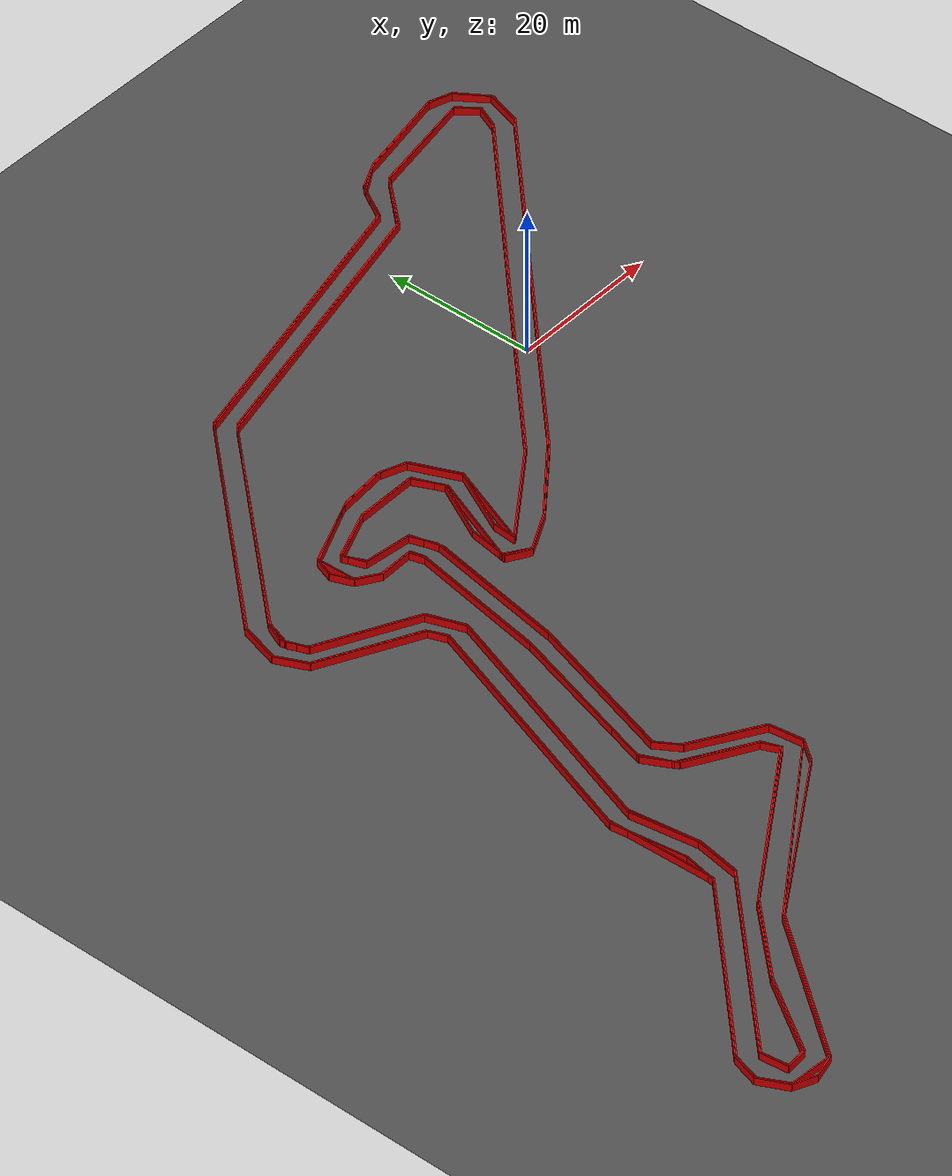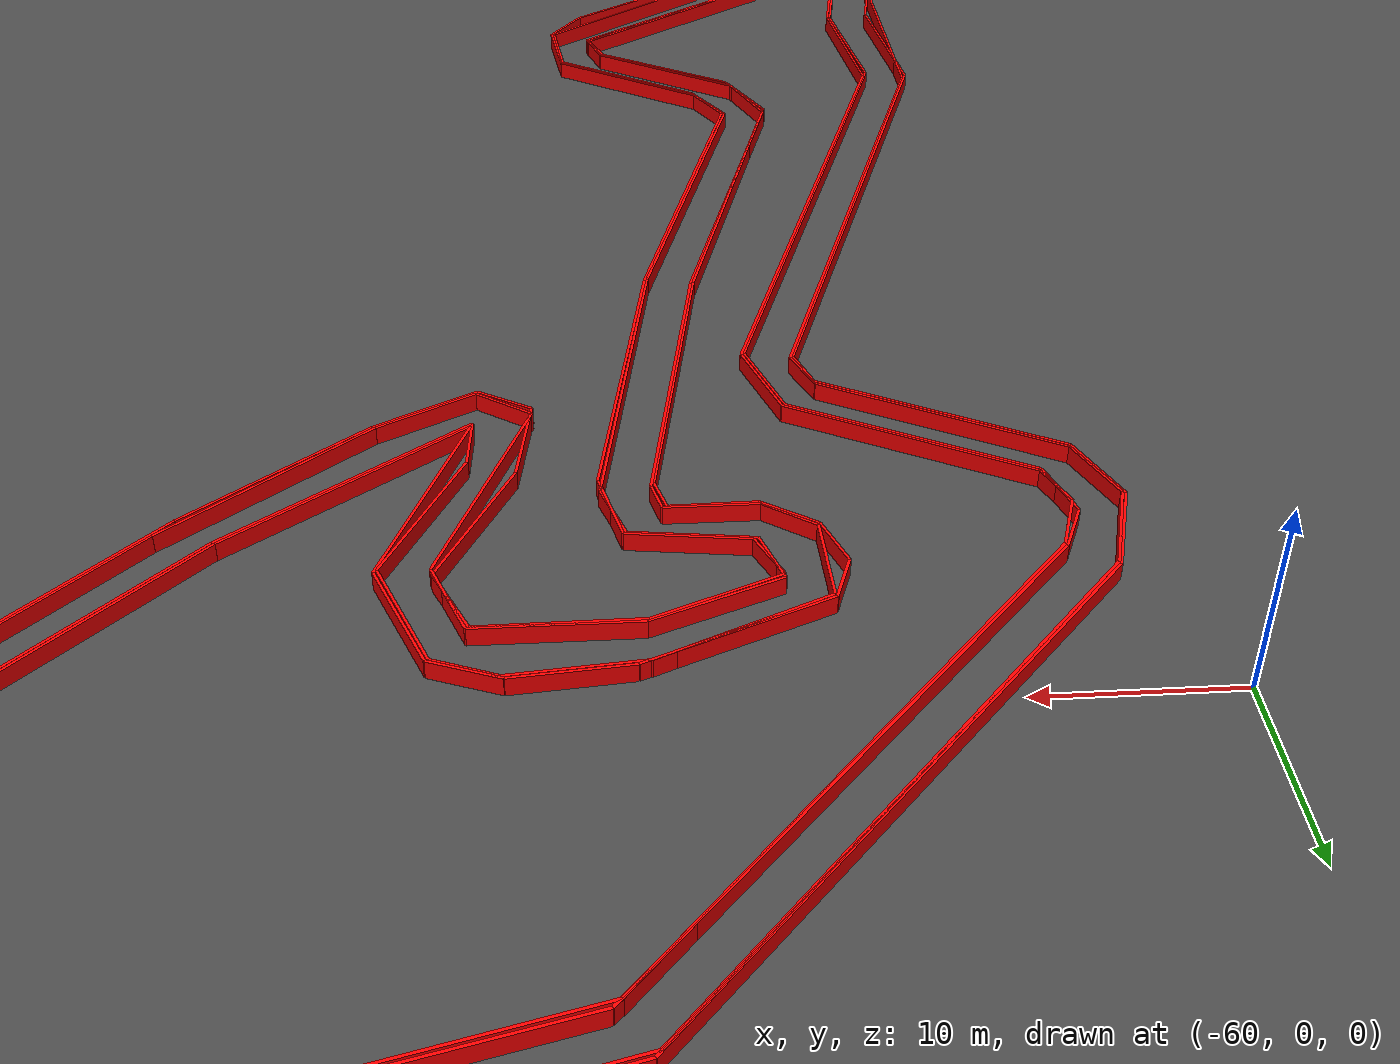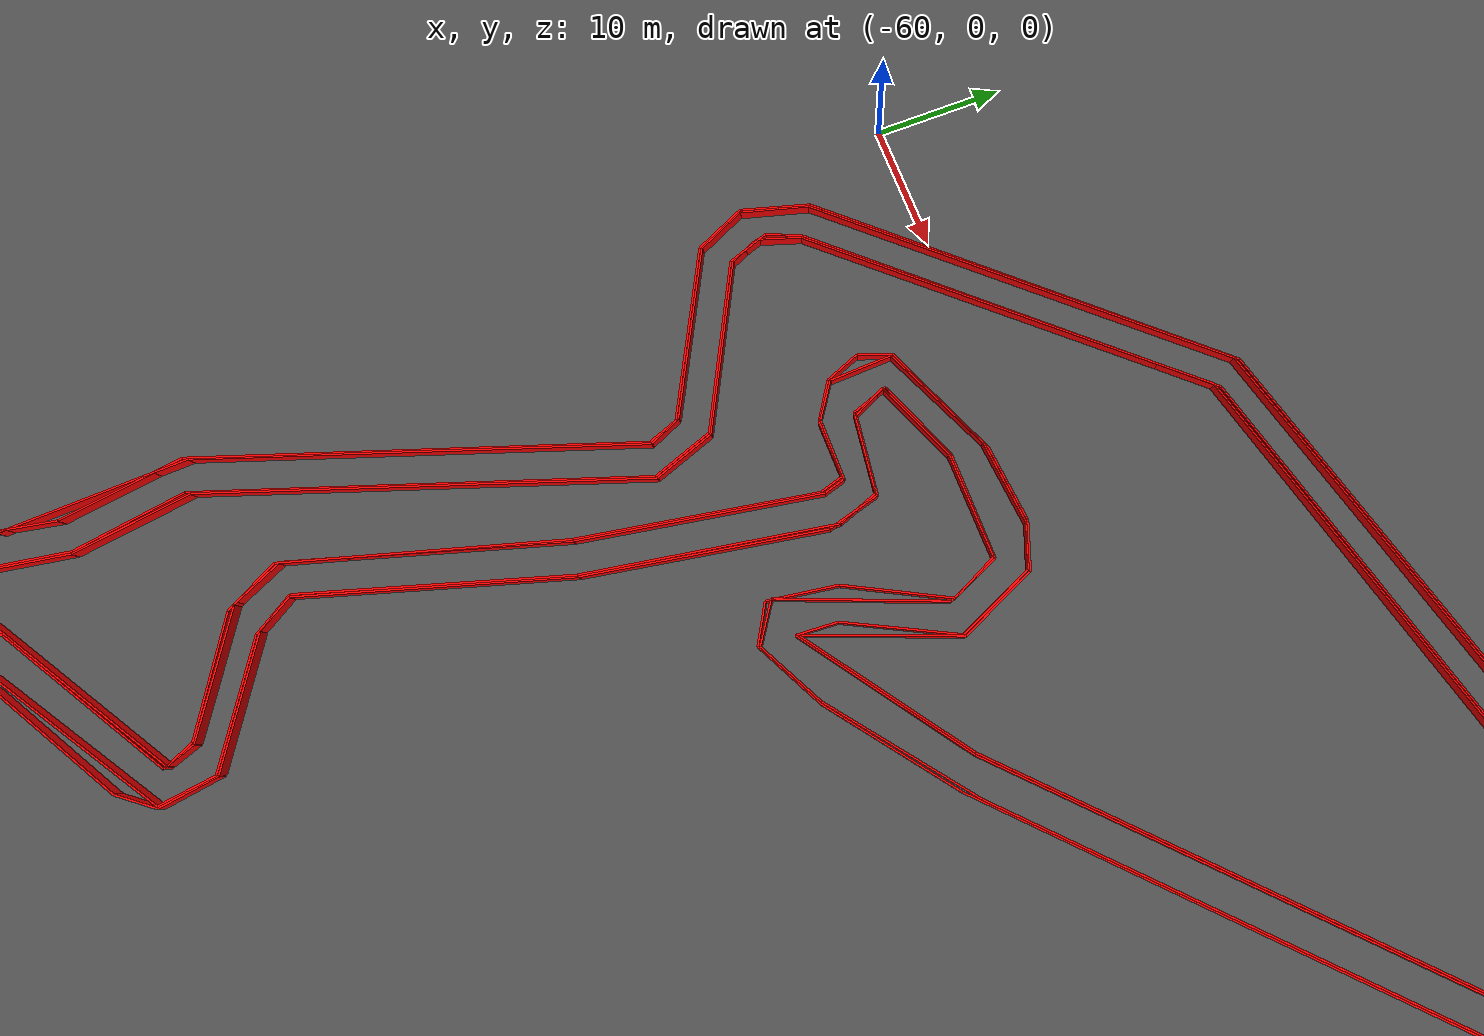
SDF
<?xml version="1.0" ?>
<sdf version="1.6">
  <world name="track_world">
    <scene>
      <ambient>0.4 0.4 0.4 1</ambient>
      <background>0.7 0.7 0.7 1</background>
      <shadows>true</shadows>
    </scene>
    <light name="sun" type="directional">
      <pose>0 0 10 0 0 0</pose>
      <diffuse>0.8 0.8 0.8 1</diffuse>
      <direction>-0.5 0.1 -0.9</direction>
    </light>
    <model name="ground_plane">
      <static>true</static>
      <link name="link">
        <collision name="collision">
          <geometry>
            <plane>
              <normal>0 0 1</normal>
              <size>1000 1000</size>
            </plane>
          </geometry>
        </collision>
        <visual name="visual">
          <geometry>
            <plane>
              <normal>0 0 1</normal>
              <size>1000 1000</size>
            </plane>
          </geometry>
          <material>
            <ambient>0.3 0.3 0.3 1</ambient>
            <diffuse>0.3 0.3 0.3 1</diffuse>
          </material>
        </visual>
      </link>
    </model>
    <model name="wall_0">
      <static>true</static>
      <pose>27.159355830790837 36.11916817799599 0.5 0 0 2.8273607545054484</pose>
      <link name="link">
        <visual name="visual">
          <geometry>
            <box>
              <size>3.1721261090316166 0.15 1.0</size>
            </box>
          </geometry>
          <material>
            <ambient>1 0 0 1</ambient>
            <diffuse>1 0 0 1</diffuse>
          </material>
        </visual>
        <collision name="collision">
          <geometry>
            <box>
              <size>3.1721261090316166 0.15 1.0</size>
            </box>
          </geometry>
        </collision>
      </link>
    </model>
    <model name="wall_1">
      <static>true</static>
      <pose>19.27796583079084 35.327258177995986 0.5 0 0 -2.94305943780296</pose>
      <link name="link">
        <visual name="visual">
          <geometry>
            <box>
              <size>13.001366777335367 0.15 1.0</size>
            </box>
          </geometry>
          <material>
            <ambient>1 0 0 1</ambient>
            <diffuse>1 0 0 1</diffuse>
          </material>
        </visual>
        <collision name="collision">
          <geometry>
            <box>
              <size>13.001366777335367 0.15 1.0</size>
            </box>
          </geometry>
        </collision>
      </link>
    </model>
    <model name="wall_2">
      <static>true</static>
      <pose>11.057185830790843 33.140078177995974 0.5 0 0 -2.6861415823389008</pose>
      <link name="link">
        <visual name="visual">
          <geometry>
            <box>
              <size>4.11505785412551 0.15 1.0</size>
            </box>
          </geometry>
          <material>
            <ambient>1 0 0 1</ambient>
            <diffuse>1 0 0 1</diffuse>
          </material>
        </visual>
        <collision name="collision">
          <geometry>
            <box>
              <size>4.11505785412551 0.15 1.0</size>
            </box>
          </geometry>
        </collision>
      </link>
    </model>
    <model name="wall_3">
      <static>true</static>
      <pose>7.814125830790843 29.897018177995974 0.5 0 0 -2.10884053462052</pose>
      <link name="link">
        <visual name="visual">
          <geometry>
            <box>
              <size>5.445407567225796 0.15 1.0</size>
            </box>
          </geometry>
          <material>
            <ambient>1 0 0 1</ambient>
            <diffuse>1 0 0 1</diffuse>
          </material>
        </visual>
        <collision name="collision">
          <geometry>
            <box>
              <size>5.445407567225796 0.15 1.0</size>
            </box>
          </geometry>
        </collision>
      </link>
    </model>
    <model name="wall_4">
      <static>true</static>
      <pose>-13.190344169209155 22.69440817799598 0.5 0 0 -2.8984247625897464</pose>
      <link name="link">
        <visual name="visual">
          <geometry>
            <box>
              <size>40.40717562552968 0.15 1.0</size>
            </box>
          </geometry>
          <material>
            <ambient>1 0 0 1</ambient>
            <diffuse>1 0 0 1</diffuse>
          </material>
        </visual>
        <collision name="collision">
          <geometry>
            <box>
              <size>40.40717562552968 0.15 1.0</size>
            </box>
          </geometry>
        </collision>
      </link>
    </model>
    <model name="wall_5">
      <static>true</static>
      <pose>-44.338804169209155 5.234678177995988 0.5 0 0 -2.3124723715907574</pose>
      <link name="link">
        <visual name="visual">
          <geometry>
            <box>
              <size>34.163844805126956 0.15 1.0</size>
            </box>
          </geometry>
          <material>
            <ambient>1 0 0 1</ambient>
            <diffuse>1 0 0 1</diffuse>
          </material>
        </visual>
        <collision name="collision">
          <geometry>
            <box>
              <size>34.163844805126956 0.15 1.0</size>
            </box>
          </geometry>
        </collision>
      </link>
    </model>
    <model name="wall_6">
      <static>true</static>
      <pose>-56.632264169209165 -9.924741822004016 0.5 0 0 -1.8568477685122147</pose>
      <link name="link">
        <visual name="visual">
          <geometry>
            <box>
              <size>5.345783219847218 0.15 1.0</size>
            </box>
          </geometry>
          <material>
            <ambient>1 0 0 1</ambient>
            <diffuse>1 0 0 1</diffuse>
          </material>
        </visual>
        <collision name="collision">
          <geometry>
            <box>
              <size>5.345783219847218 0.15 1.0</size>
            </box>
          </geometry>
        </collision>
      </link>
    </model>
    <model name="wall_7">
      <static>true</static>
      <pose>-56.48142416920916 -14.449941822004014 0.5 0 0 -1.1383885512243563</pose>
      <link name="link">
        <visual name="visual">
          <geometry>
            <box>
              <size>4.319400258369202 0.15 1.0</size>
            </box>
          </geometry>
          <material>
            <ambient>1 0 0 1</ambient>
            <diffuse>1 0 0 1</diffuse>
          </material>
        </visual>
        <collision name="collision">
          <geometry>
            <box>
              <size>4.319400258369202 0.15 1.0</size>
            </box>
          </geometry>
        </collision>
      </link>
    </model>
    <model name="wall_8">
      <static>true</static>
      <pose>-49.50507416920916 -19.503081822004013 0.5 0 0 -0.4710732150903404</pose>
      <link name="link">
        <visual name="visual">
          <geometry>
            <box>
              <size>13.626830833983373 0.15 1.0</size>
            </box>
          </geometry>
          <material>
            <ambient>1 0 0 1</ambient>
            <diffuse>1 0 0 1</diffuse>
          </material>
        </visual>
        <collision name="collision">
          <geometry>
            <box>
              <size>13.626830833983373 0.15 1.0</size>
            </box>
          </geometry>
        </collision>
      </link>
    </model>
    <model name="wall_9">
      <static>true</static>
      <pose>-43.01895416920916 -23.726601822004014 0.5 0 0 -1.2193515327913416</pose>
      <link name="link">
        <visual name="visual">
          <geometry>
            <box>
              <size>2.409902094359846 0.15 1.0</size>
            </box>
          </geometry>
          <material>
            <ambient>1 0 0 1</ambient>
            <diffuse>1 0 0 1</diffuse>
          </material>
        </visual>
        <collision name="collision">
          <geometry>
            <box>
              <size>2.409902094359846 0.15 1.0</size>
            </box>
          </geometry>
        </collision>
      </link>
    </model>
    <model name="wall_10">
      <static>true</static>
      <pose>-48.18522416920916 -40.84694182200401 0.5 0 0 -1.906630457014399</pose>
      <link name="link">
        <visual name="visual">
          <geometry>
            <box>
              <size>33.87021429445052 0.15 1.0</size>
            </box>
          </geometry>
          <material>
            <ambient>1 0 0 1</ambient>
            <diffuse>1 0 0 1</diffuse>
          </material>
        </visual>
        <collision name="collision">
          <geometry>
            <box>
              <size>33.87021429445052 0.15 1.0</size>
            </box>
          </geometry>
        </collision>
      </link>
    </model>
    <model name="wall_11">
      <static>true</static>
      <pose>-53.12523416920916 -61.54973182200402 0.5 0 0 -1.435625628145888</pose>
      <link name="link">
        <visual name="visual">
          <geometry>
            <box>
              <size>9.514286059899616 0.15 1.0</size>
            </box>
          </geometry>
          <material>
            <ambient>1 0 0 1</ambient>
            <diffuse>1 0 0 1</diffuse>
          </material>
        </visual>
        <collision name="collision">
          <geometry>
            <box>
              <size>9.514286059899616 0.15 1.0</size>
            </box>
          </geometry>
        </collision>
      </link>
    </model>
    <model name="wall_12">
      <static>true</static>
      <pose>-52.898974169209154 -68.37524182200401 0.5 0 0 -1.7647554740547904</pose>
      <link name="link">
        <visual name="visual">
          <geometry>
            <box>
              <size>4.304229377577341 0.15 1.0</size>
            </box>
          </geometry>
          <material>
            <ambient>1 0 0 1</ambient>
            <diffuse>1 0 0 1</diffuse>
          </material>
        </visual>
        <collision name="collision">
          <geometry>
            <box>
              <size>4.304229377577341 0.15 1.0</size>
            </box>
          </geometry>
        </collision>
      </link>
    </model>
    <model name="wall_13">
      <static>true</static>
      <pose>-62.74128416920916 -79.65053182200401 0.5 0 0 -2.370392319085259</pose>
      <link name="link">
        <visual name="visual">
          <geometry>
            <box>
              <size>26.294336904428693 0.15 1.0</size>
            </box>
          </geometry>
          <material>
            <ambient>1 0 0 1</ambient>
            <diffuse>1 0 0 1</diffuse>
          </material>
        </visual>
        <collision name="collision">
          <geometry>
            <box>
              <size>26.294336904428693 0.15 1.0</size>
            </box>
          </geometry>
        </collision>
      </link>
    </model>
    <model name="wall_14">
      <static>true</static>
      <pose>-72.69672416920916 -90.51101182200401 0.5 0 0 -1.872415373061138</pose>
      <link name="link">
        <visual name="visual">
          <geometry>
            <box>
              <size>3.5543550447865955 0.15 1.0</size>
            </box>
          </geometry>
          <material>
            <ambient>1 0 0 1</ambient>
            <diffuse>1 0 0 1</diffuse>
          </material>
        </visual>
        <collision name="collision">
          <geometry>
            <box>
              <size>3.5543550447865955 0.15 1.0</size>
            </box>
          </geometry>
        </collision>
      </link>
    </model>
    <model name="wall_15">
      <static>true</static>
      <pose>-72.35733416920917 -93.98033182200402 0.5 0 0 -1.1156955182267012</pose>
      <link name="link">
        <visual name="visual">
          <geometry>
            <box>
              <size>3.946419514344623 0.15 1.0</size>
            </box>
          </geometry>
          <material>
            <ambient>1 0 0 1</ambient>
            <diffuse>1 0 0 1</diffuse>
          </material>
        </visual>
        <collision name="collision">
          <geometry>
            <box>
              <size>3.946419514344623 0.15 1.0</size>
            </box>
          </geometry>
        </collision>
      </link>
    </model>
    <model name="wall_16">
      <static>true</static>
      <pose>-70.13244416920915 -96.35606182200402 0.5 0 0 -0.41822432957923056</pose>
      <link name="link">
        <visual name="visual">
          <geometry>
            <box>
              <size>2.9712034216458494 0.15 1.0</size>
            </box>
          </geometry>
          <material>
            <ambient>1 0 0 1</ambient>
            <diffuse>1 0 0 1</diffuse>
          </material>
        </visual>
        <collision name="collision">
          <geometry>
            <box>
              <size>2.9712034216458494 0.15 1.0</size>
            </box>
          </geometry>
        </collision>
      </link>
    </model>
    <model name="wall_17">
      <static>true</static>
      <pose>-67.26648416920915 -96.58232182200402 0.5 0 0 0.24497866312686303</pose>
      <link name="link">
        <visual name="visual">
          <geometry>
            <box>
              <size>3.109646262840842 0.15 1.0</size>
            </box>
          </geometry>
          <material>
            <ambient>1 0 0 1</ambient>
            <diffuse>1 0 0 1</diffuse>
          </material>
        </visual>
        <collision name="collision">
          <geometry>
            <box>
              <size>3.109646262840842 0.15 1.0</size>
            </box>
          </geometry>
        </collision>
      </link>
    </model>
    <model name="wall_18">
      <static>true</static>
      <pose>-59.15883416920916 -87.83360182200403 0.5 0 0 0.9032375815154151</pose>
      <link name="link">
        <visual name="visual">
          <geometry>
            <box>
              <size>21.319861349164537 0.15 1.0</size>
            </box>
          </geometry>
          <material>
            <ambient>1 0 0 1</ambient>
            <diffuse>1 0 0 1</diffuse>
          </material>
        </visual>
        <collision name="collision">
          <geometry>
            <box>
              <size>21.319861349164537 0.15 1.0</size>
            </box>
          </geometry>
        </collision>
      </link>
    </model>
    <model name="wall_19">
      <static>true</static>
      <pose>-42.49101416920916 -73.16441182200401 0.5 0 0 0.5589359023385937</pose>
      <link name="link">
        <visual name="visual">
          <geometry>
            <box>
              <size>23.751672762127733 0.15 1.0</size>
            </box>
          </geometry>
          <material>
            <ambient>1 0 0 1</ambient>
            <diffuse>1 0 0 1</diffuse>
          </material>
        </visual>
        <collision name="collision">
          <geometry>
            <box>
              <size>23.751672762127733 0.15 1.0</size>
            </box>
          </geometry>
        </collision>
      </link>
    </model>
    <model name="wall_20">
      <static>true</static>
      <pose>-31.441984169209157 -65.584701822004 0.5 0 0 0.9179496956941213</pose>
      <link name="link">
        <visual name="visual">
          <geometry>
            <box>
              <size>3.22811696888449 0.15 1.0</size>
            </box>
          </geometry>
          <material>
            <ambient>1 0 0 1</ambient>
            <diffuse>1 0 0 1</diffuse>
          </material>
        </visual>
        <collision name="collision">
          <geometry>
            <box>
              <size>3.22811696888449 0.15 1.0</size>
            </box>
          </geometry>
        </collision>
      </link>
    </model>
    <model name="wall_21">
      <static>true</static>
      <pose>-30.76320416920916 -62.11538182200401 0.5 0 0 1.7078625011050865</pose>
      <link name="link">
        <visual name="visual">
          <geometry>
            <box>
              <size>4.415774982854082 0.15 1.0</size>
            </box>
          </geometry>
          <material>
            <ambient>1 0 0 1</ambient>
            <diffuse>1 0 0 1</diffuse>
          </material>
        </visual>
        <collision name="collision">
          <geometry>
            <box>
              <size>4.415774982854082 0.15 1.0</size>
            </box>
          </geometry>
        </collision>
      </link>
    </model>
    <model name="wall_22">
      <static>true</static>
      <pose>-35.32611416920916 -57.363921822004016 0.5 0 0 2.5998727639351658</pose>
      <link name="link">
        <visual name="visual">
          <geometry>
            <box>
              <size>9.946579921018074 0.15 1.0</size>
            </box>
          </geometry>
          <material>
            <ambient>1 0 0 1</ambient>
            <diffuse>1 0 0 1</diffuse>
          </material>
        </visual>
        <collision name="collision">
          <geometry>
            <box>
              <size>9.946579921018074 0.15 1.0</size>
            </box>
          </geometry>
        </collision>
      </link>
    </model>
    <model name="wall_23">
      <static>true</static>
      <pose>-40.37925416920916 -53.517501822004014 0.5 0 0 2.1240906521171885</pose>
      <link name="link">
        <visual name="visual">
          <geometry>
            <box>
              <size>3.0139704230134656 0.15 1.0</size>
            </box>
          </geometry>
          <material>
            <ambient>1 0 0 1</ambient>
            <diffuse>1 0 0 1</diffuse>
          </material>
        </visual>
        <collision name="collision">
          <geometry>
            <box>
              <size>3.0139704230134656 0.15 1.0</size>
            </box>
          </geometry>
        </collision>
      </link>
    </model>
    <model name="wall_24">
      <static>true</static>
      <pose>-38.15436416920916 -42.50618182200401 0.5 0 0 1.2701199353947692</pose>
      <link name="link">
        <visual name="visual">
          <geometry>
            <box>
              <size>20.372336705680087 0.15 1.0</size>
            </box>
          </geometry>
          <material>
            <ambient>1 0 0 1</ambient>
            <diffuse>1 0 0 1</diffuse>
          </material>
        </visual>
        <collision name="collision">
          <geometry>
            <box>
              <size>20.372336705680087 0.15 1.0</size>
            </box>
          </geometry>
        </collision>
      </link>
    </model>
    <model name="wall_25">
      <static>true</static>
      <pose>-33.516034169209156 -23.87744182200401 0.5 0 0 1.3905699709421426</pose>
      <link name="link">
        <visual name="visual">
          <geometry>
            <box>
              <size>18.09215606106691 0.15 1.0</size>
            </box>
          </geometry>
          <material>
            <ambient>1 0 0 1</ambient>
            <diffuse>1 0 0 1</diffuse>
          </material>
        </visual>
        <collision name="collision">
          <geometry>
            <box>
              <size>18.09215606106691 0.15 1.0</size>
            </box>
          </geometry>
        </collision>
      </link>
    </model>
    <model name="wall_26">
      <static>true</static>
      <pose>-32.42244416920916 -12.941541822004012 0.5 0 0 1.8244704229335402</pose>
      <link name="link">
        <visual name="visual">
          <geometry>
            <box>
              <size>4.207327531438446 0.15 1.0</size>
            </box>
          </geometry>
          <material>
            <ambient>1 0 0 1</ambient>
            <diffuse>1 0 0 1</diffuse>
          </material>
        </visual>
        <collision name="collision">
          <geometry>
            <box>
              <size>4.207327531438446 0.15 1.0</size>
            </box>
          </geometry>
        </collision>
      </link>
    </model>
    <model name="wall_27">
      <static>true</static>
      <pose>-36.00489416920916 -10.528101822004018 0.5 0 0 3.0187574147118985</pose>
      <link name="link">
        <visual name="visual">
          <geometry>
            <box>
              <size>6.155399499658817 0.15 1.0</size>
            </box>
          </geometry>
          <material>
            <ambient>1 0 0 1</ambient>
            <diffuse>1 0 0 1</diffuse>
          </material>
        </visual>
        <collision name="collision">
          <geometry>
            <box>
              <size>6.155399499658817 0.15 1.0</size>
            </box>
          </geometry>
        </collision>
      </link>
    </model>
    <model name="wall_28">
      <static>true</static>
      <pose>-39.662764169209154 -8.868861822004014 0.5 0 0 2.01063890961063</pose>
      <link name="link">
        <visual name="visual">
          <geometry>
            <box>
              <size>2.834026301359966 0.15 1.0</size>
            </box>
          </geometry>
          <material>
            <ambient>1 0 0 1</ambient>
            <diffuse>1 0 0 1</diffuse>
          </material>
        </visual>
        <collision name="collision">
          <geometry>
            <box>
              <size>2.834026301359966 0.15 1.0</size>
            </box>
          </geometry>
        </collision>
      </link>
    </model>
    <model name="wall_29">
      <static>true</static>
      <pose>-37.060774169209154 -6.266871822004013 0.5 0 0 0.3906070436976856</pose>
      <link name="link">
        <visual name="visual">
          <geometry>
            <box>
              <size>6.932899146821619 0.15 1.0</size>
            </box>
          </geometry>
          <material>
            <ambient>1 0 0 1</ambient>
            <diffuse>1 0 0 1</diffuse>
          </material>
        </visual>
        <collision name="collision">
          <geometry>
            <box>
              <size>6.932899146821619 0.15 1.0</size>
            </box>
          </geometry>
        </collision>
      </link>
    </model>
    <model name="wall_30">
      <static>true</static>
      <pose>-29.820454169209157 -4.909311822004014 0.5 0 0 0.009345522307490922</pose>
      <link name="link">
        <visual name="visual">
          <geometry>
            <box>
              <size>8.070292422211233 0.15 1.0</size>
            </box>
          </geometry>
          <material>
            <ambient>1 0 0 1</ambient>
            <diffuse>1 0 0 1</diffuse>
          </material>
        </visual>
        <collision name="collision">
          <geometry>
            <box>
              <size>8.070292422211233 0.15 1.0</size>
            </box>
          </geometry>
        </collision>
      </link>
    </model>
    <model name="wall_31">
      <static>true</static>
      <pose>-24.91815416920916 -6.681681822004009 0.5 0 0 -1.1239538583091344</pose>
      <link name="link">
        <visual name="visual">
          <geometry>
            <box>
              <size>4.014299906733422 0.15 1.0</size>
            </box>
          </geometry>
          <material>
            <ambient>1 0 0 1</ambient>
            <diffuse>1 0 0 1</diffuse>
          </material>
        </visual>
        <collision name="collision">
          <geometry>
            <box>
              <size>4.014299906733422 0.15 1.0</size>
            </box>
          </geometry>
        </collision>
      </link>
    </model>
    <model name="wall_32">
      <static>true</static>
      <pose>-25.974034169209162 -12.149631822004011 0.5 0 0 -2.0548492664822398</pose>
      <link name="link">
        <visual name="visual">
          <geometry>
            <box>
              <size>8.26528877680629 0.15 1.0</size>
            </box>
          </geometry>
          <material>
            <ambient>1 0 0 1</ambient>
            <diffuse>1 0 0 1</diffuse>
          </material>
        </visual>
        <collision name="collision">
          <geometry>
            <box>
              <size>8.26528877680629 0.15 1.0</size>
            </box>
          </geometry>
        </collision>
      </link>
    </model>
    <model name="wall_33">
      <static>true</static>
      <pose>-28.312054169209162 -18.44720182200401 0.5 0 0 -1.7266645281932202</pose>
      <link name="link">
        <visual name="visual">
          <geometry>
            <box>
              <size>5.344186907696995 0.15 1.0</size>
            </box>
          </geometry>
          <material>
            <ambient>1 0 0 1</ambient>
            <diffuse>1 0 0 1</diffuse>
          </material>
        </visual>
        <collision name="collision">
          <geometry>
            <box>
              <size>5.344186907696995 0.15 1.0</size>
            </box>
          </geometry>
        </collision>
      </link>
    </model>
    <model name="wall_34">
      <static>true</static>
      <pose>-27.33159416920916 -21.87881182200401 0.5 0 0 -0.5162306706117475</pose>
      <link name="link">
        <visual name="visual">
          <geometry>
            <box>
              <size>3.208675627731798 0.15 1.0</size>
            </box>
          </geometry>
          <material>
            <ambient>1 0 0 1</ambient>
            <diffuse>1 0 0 1</diffuse>
          </material>
        </visual>
        <collision name="collision">
          <geometry>
            <box>
              <size>3.208675627731798 0.15 1.0</size>
            </box>
          </geometry>
        </collision>
      </link>
    </model>
    <model name="wall_35">
      <static>true</static>
      <pose>-23.29662416920916 -21.313161822004012 0.5 0 0 0.47501075626509703</pose>
      <link name="link">
        <visual name="visual">
          <geometry>
            <box>
              <size>5.936660759585303 0.15 1.0</size>
            </box>
          </geometry>
          <material>
            <ambient>1 0 0 1</ambient>
            <diffuse>1 0 0 1</diffuse>
          </material>
        </visual>
        <collision name="collision">
          <geometry>
            <box>
              <size>5.936660759585303 0.15 1.0</size>
            </box>
          </geometry>
        </collision>
      </link>
    </model>
    <model name="wall_36">
      <static>true</static>
      <pose>-16.16943416920916 -16.523991822004014 0.5 0 0 0.652846631100774</pose>
      <link name="link">
        <visual name="visual">
          <geometry>
            <box>
              <size>11.298409391095722 0.15 1.0</size>
            </box>
          </geometry>
          <material>
            <ambient>1 0 0 1</ambient>
            <diffuse>1 0 0 1</diffuse>
          </material>
        </visual>
        <collision name="collision">
          <geometry>
            <box>
              <size>11.298409391095722 0.15 1.0</size>
            </box>
          </geometry>
        </collision>
      </link>
    </model>
    <model name="wall_37">
      <static>true</static>
      <pose>9.02084583079084 6.893918177995985 0.5 0 0 0.7677910859479851</pose>
      <link name="link">
        <visual name="visual">
          <geometry>
            <box>
              <size>57.55198350966194 0.15 1.0</size>
            </box>
          </geometry>
          <material>
            <ambient>1 0 0 1</ambient>
            <diffuse>1 0 0 1</diffuse>
          </material>
        </visual>
        <collision name="collision">
          <geometry>
            <box>
              <size>57.55198350966194 0.15 1.0</size>
            </box>
          </geometry>
        </collision>
      </link>
    </model>
    <model name="wall_38">
      <static>true</static>
      <pose>30.515545830790835 29.25594817799599 0.5 0 0 1.249045772398257</pose>
      <link name="link">
        <visual name="visual">
          <geometry>
            <box>
              <size>5.008478603727887 0.15 1.0</size>
            </box>
          </geometry>
          <material>
            <ambient>1 0 0 1</ambient>
            <diffuse>1 0 0 1</diffuse>
          </material>
        </visual>
        <collision name="collision">
          <geometry>
            <box>
              <size>5.008478603727887 0.15 1.0</size>
            </box>
          </geometry>
        </collision>
      </link>
    </model>
    <model name="wall_39">
      <static>true</static>
      <pose>29.987605830790834 33.630308177995985 0.5 0 0 2.1544321458720583</pose>
      <link name="link">
        <visual name="visual">
          <geometry>
            <box>
              <size>4.790209139233882 0.15 1.0</size>
            </box>
          </geometry>
          <material>
            <ambient>1 0 0 1</ambient>
            <diffuse>1 0 0 1</diffuse>
          </material>
        </visual>
        <collision name="collision">
          <geometry>
            <box>
              <size>4.790209139233882 0.15 1.0</size>
            </box>
          </geometry>
        </collision>
      </link>
    </model>
    <model name="wall_40">
      <static>true</static>
      <pose>29.83676583079084 33.630308177995985 0.5 0 0 -0.9693416199346254</pose>
      <link name="link">
        <visual name="visual">
          <geometry>
            <box>
              <size>4.665079088975899 0.15 1.0</size>
            </box>
          </geometry>
          <material>
            <ambient>1 0 0 1</ambient>
            <diffuse>1 0 0 1</diffuse>
          </material>
        </visual>
        <collision name="collision">
          <geometry>
            <box>
              <size>4.665079088975899 0.15 1.0</size>
            </box>
          </geometry>
        </collision>
      </link>
    </model>
    <model name="wall_41">
      <static>true</static>
      <pose>30.402415830790844 29.369078177995974 0.5 0 0 -1.8828384483574288</pose>
      <link name="link">
        <visual name="visual">
          <geometry>
            <box>
              <size>4.913310558228534 0.15 1.0</size>
            </box>
          </geometry>
          <material>
            <ambient>1 0 0 1</ambient>
            <diffuse>1 0 0 1</diffuse>
          </material>
        </visual>
        <collision name="collision">
          <geometry>
            <box>
              <size>4.913310558228534 0.15 1.0</size>
            </box>
          </geometry>
        </collision>
      </link>
    </model>
    <model name="wall_42">
      <static>true</static>
      <pose>9.435655830790843 7.49727817799598 0.5 0 0 -2.3732706290907037</pose>
      <link name="link">
        <visual name="visual">
          <geometry>
            <box>
              <size>56.21800931523634 0.15 1.0</size>
            </box>
          </geometry>
          <material>
            <ambient>1 0 0 1</ambient>
            <diffuse>1 0 0 1</diffuse>
          </material>
        </visual>
        <collision name="collision">
          <geometry>
            <box>
              <size>56.21800931523634 0.15 1.0</size>
            </box>
          </geometry>
        </collision>
      </link>
    </model>
    <model name="wall_43">
      <static>true</static>
      <pose>-15.792334169209163 -15.958341822004016 0.5 0 0 -2.4779520879828056</pose>
      <link name="link">
        <visual name="visual">
          <geometry>
            <box>
              <size>12.733478247595988 0.15 1.0</size>
            </box>
          </geometry>
          <material>
            <ambient>1 0 0 1</ambient>
            <diffuse>1 0 0 1</diffuse>
          </material>
        </visual>
        <collision name="collision">
          <geometry>
            <box>
              <size>12.733478247595988 0.15 1.0</size>
            </box>
          </geometry>
        </collision>
      </link>
    </model>
    <model name="wall_44">
      <static>true</static>
      <pose>-23.334334169209164 -21.200031822004014 0.5 0 0 -2.6601954295324908</pose>
      <link name="link">
        <visual name="visual">
          <geometry>
            <box>
              <size>5.7010735786867315 0.15 1.0</size>
            </box>
          </geometry>
          <material>
            <ambient>1 0 0 1</ambient>
            <diffuse>1 0 0 1</diffuse>
          </material>
        </visual>
        <collision name="collision">
          <geometry>
            <box>
              <size>5.7010735786867315 0.15 1.0</size>
            </box>
          </geometry>
        </collision>
      </link>
    </model>
    <model name="wall_45">
      <static>true</static>
      <pose>-27.293884169209164 -21.577131822004013 0.5 0 0 2.5596875354499096</pose>
      <link name="link">
        <visual name="visual">
          <geometry>
            <box>
              <size>3.4305738545613593 0.15 1.0</size>
            </box>
          </geometry>
          <material>
            <ambient>1 0 0 1</ambient>
            <diffuse>1 0 0 1</diffuse>
          </material>
        </visual>
        <collision name="collision">
          <geometry>
            <box>
              <size>3.4305738545613593 0.15 1.0</size>
            </box>
          </geometry>
        </collision>
      </link>
    </model>
    <model name="wall_46">
      <static>true</static>
      <pose>-26.35113416920916 -14.751621822004012 0.5 0 0 1.1869787035063275</pose>
      <link name="link">
        <visual name="visual">
          <geometry>
            <box>
              <size>12.688728580988732 0.15 1.0</size>
            </box>
          </geometry>
          <material>
            <ambient>1 0 0 1</ambient>
            <diffuse>1 0 0 1</diffuse>
          </material>
        </visual>
        <collision name="collision">
          <geometry>
            <box>
              <size>12.688728580988732 0.15 1.0</size>
            </box>
          </geometry>
        </collision>
      </link>
    </model>
    <model name="wall_47">
      <static>true</static>
      <pose>-24.805024169209155 -6.832521822004011 0.5 0 0 1.9576720445259248</pose>
      <link name="link">
        <visual name="visual">
          <geometry>
            <box>
              <size>4.397703919092316 0.15 1.0</size>
            </box>
          </geometry>
          <material>
            <ambient>1 0 0 1</ambient>
            <diffuse>1 0 0 1</diffuse>
          </material>
        </visual>
        <collision name="collision">
          <geometry>
            <box>
              <size>4.397703919092316 0.15 1.0</size>
            </box>
          </geometry>
        </collision>
      </link>
    </model>
    <model name="wall_48">
      <static>true</static>
      <pose>-29.70732416920916 -4.796181822004016 0.5 0 0 3.141592653589793</pose>
      <link name="link">
        <visual name="visual">
          <geometry>
            <box>
              <size>8.14536000000001 0.15 1.0</size>
            </box>
          </geometry>
          <material>
            <ambient>1 0 0 1</ambient>
            <diffuse>1 0 0 1</diffuse>
          </material>
        </visual>
        <collision name="collision">
          <geometry>
            <box>
              <size>8.14536000000001 0.15 1.0</size>
            </box>
          </geometry>
        </collision>
      </link>
    </model>
    <model name="wall_49">
      <static>true</static>
      <pose>-37.023064169209164 -6.078321822004014 0.5 0 0 -2.76510231914327</pose>
      <link name="link">
        <visual name="visual">
          <geometry>
            <box>
              <size>6.974617163171029 0.15 1.0</size>
            </box>
          </geometry>
          <material>
            <ambient>1 0 0 1</ambient>
            <diffuse>1 0 0 1</diffuse>
          </material>
        </visual>
        <collision name="collision">
          <geometry>
            <box>
              <size>6.974617163171029 0.15 1.0</size>
            </box>
          </geometry>
        </collision>
      </link>
    </model>
    <model name="wall_50">
      <static>true</static>
      <pose>-39.77589416920915 -8.793441822004013 0.5 0 0 -1.2411719193741537</pose>
      <link name="link">
        <visual name="visual">
          <geometry>
            <box>
              <size>3.0290309561310216 0.15 1.0</size>
            </box>
          </geometry>
          <material>
            <ambient>1 0 0 1</ambient>
            <diffuse>1 0 0 1</diffuse>
          </material>
        </visual>
        <collision name="collision">
          <geometry>
            <box>
              <size>3.0290309561310216 0.15 1.0</size>
            </box>
          </geometry>
        </collision>
      </link>
    </model>
    <model name="wall_51">
      <static>true</static>
      <pose>-36.19344416920916 -10.603521822004012 0.5 0 0 -0.12135200057076334</pose>
      <link name="link">
        <visual name="visual">
          <geometry>
            <box>
              <size>6.230258080818157 0.15 1.0</size>
            </box>
          </geometry>
          <material>
            <ambient>1 0 0 1</ambient>
            <diffuse>1 0 0 1</diffuse>
          </material>
        </visual>
        <collision name="collision">
          <geometry>
            <box>
              <size>6.230258080818157 0.15 1.0</size>
            </box>
          </geometry>
        </collision>
      </link>
    </model>
    <model name="wall_52">
      <static>true</static>
      <pose>-32.53557416920916 -12.564441822004014 0.5 0 0 -1.227772386374195</pose>
      <link name="link">
        <visual name="visual">
          <geometry>
            <box>
              <size>3.363596714768289 0.15 1.0</size>
            </box>
          </geometry>
          <material>
            <ambient>1 0 0 1</ambient>
            <diffuse>1 0 0 1</diffuse>
          </material>
        </visual>
        <collision name="collision">
          <geometry>
            <box>
              <size>3.363596714768289 0.15 1.0</size>
            </box>
          </geometry>
        </collision>
      </link>
    </model>
    <model name="wall_53">
      <static>true</static>
      <pose>-33.62916416920916 -23.500341822004017 0.5 0 0 -1.7463884887450765</pose>
      <link name="link">
        <visual name="visual">
          <geometry>
            <box>
              <size>18.996260442939818 0.15 1.0</size>
            </box>
          </geometry>
          <material>
            <ambient>1 0 0 1</ambient>
            <diffuse>1 0 0 1</diffuse>
          </material>
        </visual>
        <collision name="collision">
          <geometry>
            <box>
              <size>18.996260442939818 0.15 1.0</size>
            </box>
          </geometry>
        </collision>
      </link>
    </model>
    <model name="wall_54">
      <static>true</static>
      <pose>-38.30520416920916 -42.50618182200402 0.5 0 0 -1.873681195169868</pose>
      <link name="link">
        <visual name="visual">
          <geometry>
            <box>
              <size>20.22831326409594 0.15 1.0</size>
            </box>
          </geometry>
          <material>
            <ambient>1 0 0 1</ambient>
            <diffuse>1 0 0 1</diffuse>
          </material>
        </visual>
        <collision name="collision">
          <geometry>
            <box>
              <size>20.22831326409594 0.15 1.0</size>
            </box>
          </geometry>
        </collision>
      </link>
    </model>
    <model name="wall_55">
      <static>true</static>
      <pose>-40.37925416920916 -53.63063182200402 0.5 0 0 -1.0007558630951867</pose>
      <link name="link">
        <visual name="visual">
          <geometry>
            <box>
              <size>3.493826921070936 0.15 1.0</size>
            </box>
          </geometry>
          <material>
            <ambient>1 0 0 1</ambient>
            <diffuse>1 0 0 1</diffuse>
          </material>
        </visual>
        <collision name="collision">
          <geometry>
            <box>
              <size>3.493826921070936 0.15 1.0</size>
            </box>
          </geometry>
        </collision>
      </link>
    </model>
    <model name="wall_56">
      <static>true</static>
      <pose>-35.28840416920916 -57.59018182200401 0.5 0 0 -0.540419500270584</pose>
      <link name="link">
        <visual name="visual">
          <geometry>
            <box>
              <size>9.674948622003114 0.15 1.0</size>
            </box>
          </geometry>
          <material>
            <ambient>1 0 0 1</ambient>
            <diffuse>1 0 0 1</diffuse>
          </material>
        </visual>
        <collision name="collision">
          <geometry>
            <box>
              <size>9.674948622003114 0.15 1.0</size>
            </box>
          </geometry>
        </collision>
      </link>
    </model>
    <model name="wall_57">
      <static>true</static>
      <pose>-30.87633416920916 -62.19080182200401 0.5 0 0 -1.4464413322481349</pose>
      <link name="link">
        <visual name="visual">
          <geometry>
            <box>
              <size>4.25638835563673 0.15 1.0</size>
            </box>
          </geometry>
          <material>
            <ambient>1 0 0 1</ambient>
            <diffuse>1 0 0 1</diffuse>
          </material>
        </visual>
        <collision name="collision">
          <geometry>
            <box>
              <size>4.25638835563673 0.15 1.0</size>
            </box>
          </geometry>
        </collision>
      </link>
    </model>
    <model name="wall_58">
      <static>true</static>
      <pose>-41.69910416920916 -71.88227182200401 0.5 0 0 -2.5419083384519885</pose>
      <link name="link">
        <visual name="visual">
          <geometry>
            <box>
              <size>26.860216492925 0.15 1.0</size>
            </box>
          </geometry>
          <material>
            <ambient>1 0 0 1</ambient>
            <diffuse>1 0 0 1</diffuse>
          </material>
        </visual>
        <collision name="collision">
          <geometry>
            <box>
              <size>26.860216492925 0.15 1.0</size>
            </box>
          </geometry>
        </collision>
      </link>
    </model>
    <model name="wall_59">
      <static>true</static>
      <pose>-59.34738416920916 -87.79589182200402 0.5 0 0 -2.237763966398179</pose>
      <link name="link">
        <visual name="visual">
          <geometry>
            <box>
              <size>21.213944759021125 0.15 1.0</size>
            </box>
          </geometry>
          <material>
            <ambient>1 0 0 1</ambient>
            <diffuse>1 0 0 1</diffuse>
          </material>
        </visual>
        <collision name="collision">
          <geometry>
            <box>
              <size>21.213944759021125 0.15 1.0</size>
            </box>
          </geometry>
        </collision>
      </link>
    </model>
    <model name="wall_60">
      <static>true</static>
      <pose>-68.62404416920916 -95.90354182200402 0.5 0 0 3.058451421701353</pose>
      <link name="link">
        <visual name="visual">
          <geometry>
            <box>
              <size>5.4490623787950865 0.15 1.0</size>
            </box>
          </geometry>
          <material>
            <ambient>1 0 0 1</ambient>
            <diffuse>1 0 0 1</diffuse>
          </material>
        </visual>
        <collision name="collision">
          <geometry>
            <box>
              <size>5.4490623787950865 0.15 1.0</size>
            </box>
          </geometry>
        </collision>
      </link>
    </model>
    <model name="wall_61">
      <static>true</static>
      <pose>-72.20649416920915 -94.01804182200402 0.5 0 0 2.0524600043497583</pose>
      <link name="link">
        <visual name="visual">
          <geometry>
            <box>
              <size>3.744509958058607 0.15 1.0</size>
            </box>
          </geometry>
          <material>
            <ambient>1 0 0 1</ambient>
            <diffuse>1 0 0 1</diffuse>
          </material>
        </visual>
        <collision name="collision">
          <geometry>
            <box>
              <size>3.744509958058607 0.15 1.0</size>
            </box>
          </geometry>
        </collision>
      </link>
    </model>
    <model name="wall_62">
      <static>true</static>
      <pose>-72.58359416920916 -90.66185182200401 0.5 0 0 1.2895641248766032</pose>
      <link name="link">
        <visual name="visual">
          <geometry>
            <box>
              <size>3.5326843931492102 0.15 1.0</size>
            </box>
          </geometry>
          <material>
            <ambient>1 0 0 1</ambient>
            <diffuse>1 0 0 1</diffuse>
          </material>
        </visual>
        <collision name="collision">
          <geometry>
            <box>
              <size>3.5326843931492102 0.15 1.0</size>
            </box>
          </geometry>
        </collision>
      </link>
    </model>
    <model name="wall_63">
      <static>true</static>
      <pose>-62.62815416920917 -79.725951822004 0.5 0 0 0.7733019792002686</pose>
      <link name="link">
        <visual name="visual">
          <geometry>
            <box>
              <size>26.453612036665245 0.15 1.0</size>
            </box>
          </geometry>
          <material>
            <ambient>1 0 0 1</ambient>
            <diffuse>1 0 0 1</diffuse>
          </material>
        </visual>
        <collision name="collision">
          <geometry>
            <box>
              <size>26.453612036665245 0.15 1.0</size>
            </box>
          </geometry>
        </collision>
      </link>
    </model>
    <model name="wall_64">
      <static>true</static>
      <pose>-53.35149416920916 -63.47294182200401 0.5 0 0 1.5976715748796535</pose>
      <link name="link">
        <visual name="visual">
          <geometry>
            <box>
              <size>14.033187633050433 0.15 1.0</size>
            </box>
          </geometry>
          <material>
            <ambient>1 0 0 1</ambient>
            <diffuse>1 0 0 1</diffuse>
          </material>
        </visual>
        <collision name="collision">
          <geometry>
            <box>
              <size>14.033187633050433 0.15 1.0</size>
            </box>
          </geometry>
        </collision>
      </link>
    </model>
    <model name="wall_65">
      <static>true</static>
      <pose>-47.99667416920916 -40.620681822004016 0.5 0 0 1.2341215074081695</pose>
      <link name="link">
        <visual name="visual">
          <geometry>
            <box>
              <size>33.560544107442595 0.15 1.0</size>
            </box>
          </geometry>
          <material>
            <ambient>1 0 0 1</ambient>
            <diffuse>1 0 0 1</diffuse>
          </material>
        </visual>
        <collision name="collision">
          <geometry>
            <box>
              <size>33.560544107442595 0.15 1.0</size>
            </box>
          </geometry>
        </collision>
      </link>
    </model>
    <model name="wall_66">
      <static>true</static>
      <pose>-42.98124416920916 -23.57576182200401 0.5 0 0 1.983206768392281</pose>
      <link name="link">
        <visual name="visual">
          <geometry>
            <box>
              <size>2.634307348811074 0.15 1.0</size>
            </box>
          </geometry>
          <material>
            <ambient>1 0 0 1</ambient>
            <diffuse>1 0 0 1</diffuse>
          </material>
        </visual>
        <collision name="collision">
          <geometry>
            <box>
              <size>2.634307348811074 0.15 1.0</size>
            </box>
          </geometry>
        </collision>
      </link>
    </model>
    <model name="wall_67">
      <static>true</static>
      <pose>-49.50507416920916 -19.314531822004014 0.5 0 0 2.670426389276684</pose>
      <link name="link">
        <visual name="visual">
          <geometry>
            <box>
              <size>13.458191294850879 0.15 1.0</size>
            </box>
          </geometry>
          <material>
            <ambient>1 0 0 1</ambient>
            <diffuse>1 0 0 1</diffuse>
          </material>
        </visual>
        <collision name="collision">
          <geometry>
            <box>
              <size>13.458191294850879 0.15 1.0</size>
            </box>
          </geometry>
        </collision>
      </link>
    </model>
    <model name="wall_68">
      <static>true</static>
      <pose>-56.368294169209165 -14.412231822004017 0.5 0 0 2.009655625758402</pose>
      <link name="link">
        <visual name="visual">
          <geometry>
            <box>
              <size>4.08244496006989 0.15 1.0</size>
            </box>
          </geometry>
          <material>
            <ambient>1 0 0 1</ambient>
            <diffuse>1 0 0 1</diffuse>
          </material>
        </visual>
        <collision name="collision">
          <geometry>
            <box>
              <size>4.08244496006989 0.15 1.0</size>
            </box>
          </geometry>
        </collision>
      </link>
    </model>
    <model name="wall_69">
      <static>true</static>
      <pose>-56.51913416920916 -10.037871822004014 0.5 0 0 1.2944690518198312</pose>
      <link name="link">
        <visual name="visual">
          <geometry>
            <box>
              <size>5.2523952193261305 0.15 1.0</size>
            </box>
          </geometry>
          <material>
            <ambient>1 0 0 1</ambient>
            <diffuse>1 0 0 1</diffuse>
          </material>
        </visual>
        <collision name="collision">
          <geometry>
            <box>
              <size>5.2523952193261305 0.15 1.0</size>
            </box>
          </geometry>
        </collision>
      </link>
    </model>
    <model name="wall_70">
      <static>true</static>
      <pose>-44.414224169209156 5.008418177995985 0.5 0 0 0.8326815064915635</pose>
      <link name="link">
        <visual name="visual">
          <geometry>
            <box>
              <size>33.84904719337312 0.15 1.0</size>
            </box>
          </geometry>
          <material>
            <ambient>1 0 0 1</ambient>
            <diffuse>1 0 0 1</diffuse>
          </material>
        </visual>
        <collision name="collision">
          <geometry>
            <box>
              <size>33.84904719337312 0.15 1.0</size>
            </box>
          </geometry>
        </collision>
      </link>
    </model>
    <model name="wall_71">
      <static>true</static>
      <pose>-13.303474169209153 22.468148177995985 0.5 0 0 0.2454285056516268</pose>
      <link name="link">
        <visual name="visual">
          <geometry>
            <box>
              <size>40.66320201012213 0.15 1.0</size>
            </box>
          </geometry>
          <material>
            <ambient>1 0 0 1</ambient>
            <diffuse>1 0 0 1</diffuse>
          </material>
        </visual>
        <collision name="collision">
          <geometry>
            <box>
              <size>40.66320201012213 0.15 1.0</size>
            </box>
          </geometry>
        </collision>
      </link>
    </model>
    <model name="wall_72">
      <static>true</static>
      <pose>7.587865830790847 29.482208177995986 0.5 0 0 1.0575440539286356</pose>
      <link name="link">
        <visual name="visual">
          <geometry>
            <box>
              <size>4.761624841417055 0.15 1.0</size>
            </box>
          </geometry>
          <material>
            <ambient>1 0 0 1</ambient>
            <diffuse>1 0 0 1</diffuse>
          </material>
        </visual>
        <collision name="collision">
          <geometry>
            <box>
              <size>4.761624841417055 0.15 1.0</size>
            </box>
          </geometry>
        </collision>
      </link>
    </model>
    <model name="wall_73">
      <static>true</static>
      <pose>10.566955830790846 32.64984817799599 0.5 0 0 0.543477594713046</pose>
      <link name="link">
        <visual name="visual">
          <geometry>
            <box>
              <size>4.229576193662911 0.15 1.0</size>
            </box>
          </geometry>
          <material>
            <ambient>1 0 0 1</ambient>
            <diffuse>1 0 0 1</diffuse>
          </material>
        </visual>
        <collision name="collision">
          <geometry>
            <box>
              <size>4.229576193662911 0.15 1.0</size>
            </box>
          </geometry>
        </collision>
      </link>
    </model>
    <model name="wall_74">
      <static>true</static>
      <pose>18.900865830790842 35.10099817799599 0.5 0 0 0.20516454893532557</pose>
      <link name="link">
        <visual name="visual">
          <geometry>
            <box>
              <size>13.327164292901912 0.15 1.0</size>
            </box>
          </geometry>
          <material>
            <ambient>1 0 0 1</ambient>
            <diffuse>1 0 0 1</diffuse>
          </material>
        </visual>
        <collision name="collision">
          <geometry>
            <box>
              <size>13.327164292901912 0.15 1.0</size>
            </box>
          </geometry>
        </collision>
      </link>
    </model>
    <model name="wall_75">
      <static>true</static>
      <pose>26.970805830790837 36.00603817799599 0.5 0 0 -0.284730438522708</pose>
      <link name="link">
        <visual name="visual">
          <geometry>
            <box>
              <size>3.2219438123592345 0.15 1.0</size>
            </box>
          </geometry>
          <material>
            <ambient>1 0 0 1</ambient>
            <diffuse>1 0 0 1</diffuse>
          </material>
        </visual>
        <collision name="collision">
          <geometry>
            <box>
              <size>3.2219438123592345 0.15 1.0</size>
            </box>
          </geometry>
        </collision>
      </link>
    </model>
    <model name="wall_76">
      <static>true</static>
      <pose>19.504225830790837 32.38587817799599 0.5 0 0 -2.9590328004588855</pose>
      <link name="link">
        <visual name="visual">
          <geometry>
            <box>
              <size>14.955426581157763 0.15 1.0</size>
            </box>
          </geometry>
          <material>
            <ambient>1 0 0 1</ambient>
            <diffuse>1 0 0 1</diffuse>
          </material>
        </visual>
        <collision name="collision">
          <geometry>
            <box>
              <size>14.955426581157763 0.15 1.0</size>
            </box>
          </geometry>
        </collision>
      </link>
    </model>
    <model name="wall_77">
      <static>true</static>
      <pose>9.322525830790838 27.936098177995987 0.5 0 0 -2.311638012056135</pose>
      <link name="link">
        <visual name="visual">
          <geometry>
            <box>
              <size>8.381127034212037 0.15 1.0</size>
            </box>
          </geometry>
          <material>
            <ambient>1 0 0 1</ambient>
            <diffuse>1 0 0 1</diffuse>
          </material>
        </visual>
        <collision name="collision">
          <geometry>
            <box>
              <size>8.381127034212037 0.15 1.0</size>
            </box>
          </geometry>
        </collision>
      </link>
    </model>
    <model name="wall_78">
      <static>true</static>
      <pose>-12.436144169209157 20.24325817799599 0.5 0 0 -2.903186665767688</pose>
      <link name="link">
        <visual name="visual">
          <geometry>
            <box>
              <size>38.96288006607314 0.15 1.0</size>
            </box>
          </geometry>
          <material>
            <ambient>1 0 0 1</ambient>
            <diffuse>1 0 0 1</diffuse>
          </material>
        </visual>
        <collision name="collision">
          <geometry>
            <box>
              <size>38.96288006607314 0.15 1.0</size>
            </box>
          </geometry>
        </collision>
      </link>
    </model>
    <model name="wall_79">
      <static>true</static>
      <pose>-42.528724169209156 3.424598177995989 0.5 0 0 -2.3110638651375957</pose>
      <link name="link">
        <visual name="visual">
          <geometry>
            <box>
              <size>33.098297074453846 0.15 1.0</size>
            </box>
          </geometry>
          <material>
            <ambient>1 0 0 1</ambient>
            <diffuse>1 0 0 1</diffuse>
          </material>
        </visual>
        <collision name="collision">
          <geometry>
            <box>
              <size>33.098297074453846 0.15 1.0</size>
            </box>
          </geometry>
        </collision>
      </link>
    </model>
    <model name="wall_80">
      <static>true</static>
      <pose>-54.25653416920916 -10.075581822004011 0.5 0 0 -1.9862884227357887</pose>
      <link name="link">
        <visual name="visual">
          <geometry>
            <box>
              <size>2.8027435859171974 0.15 1.0</size>
            </box>
          </geometry>
          <material>
            <ambient>1 0 0 1</ambient>
            <diffuse>1 0 0 1</diffuse>
          </material>
        </visual>
        <collision name="collision">
          <geometry>
            <box>
              <size>2.8027435859171974 0.15 1.0</size>
            </box>
          </geometry>
        </collision>
      </link>
    </model>
    <model name="wall_81">
      <static>true</static>
      <pose>-54.25653416920916 -12.97925182200401 0.5 0 0 -1.2351577764672865</pose>
      <link name="link">
        <visual name="visual">
          <geometry>
            <box>
              <size>3.434716560882427 0.15 1.0</size>
            </box>
          </geometry>
          <material>
            <ambient>1 0 0 1</ambient>
            <diffuse>1 0 0 1</diffuse>
          </material>
        </visual>
        <collision name="collision">
          <geometry>
            <box>
              <size>3.434716560882427 0.15 1.0</size>
            </box>
          </geometry>
        </collision>
      </link>
    </model>
    <model name="wall_82">
      <static>true</static>
      <pose>-47.69499416920915 -17.617581822004013 0.5 0 0 -0.46616016652765085</pose>
      <link name="link">
        <visual name="visual">
          <geometry>
            <box>
              <size>13.424124423156991 0.15 1.0</size>
            </box>
          </geometry>
          <material>
            <ambient>1 0 0 1</ambient>
            <diffuse>1 0 0 1</diffuse>
          </material>
        </visual>
        <collision name="collision">
          <geometry>
            <box>
              <size>13.424124423156991 0.15 1.0</size>
            </box>
          </geometry>
        </collision>
      </link>
    </model>
    <model name="wall_83">
      <static>true</static>
      <pose>-40.86948416920916 -22.972401822004016 0.5 0 0 -1.2298173732985478</pose>
      <link name="link">
        <visual name="visual">
          <geometry>
            <box>
              <size>4.961696026481267 0.15 1.0</size>
            </box>
          </geometry>
          <material>
            <ambient>1 0 0 1</ambient>
            <diffuse>1 0 0 1</diffuse>
          </material>
        </visual>
        <collision name="collision">
          <geometry>
            <box>
              <size>4.961696026481267 0.15 1.0</size>
            </box>
          </geometry>
        </collision>
      </link>
    </model>
    <model name="wall_84">
      <static>true</static>
      <pose>-45.62094416920916 -41.29946182200402 0.5 0 0 -1.906630457014399</pose>
      <link name="link">
        <visual name="visual">
          <geometry>
            <box>
              <size>33.87021429445051 0.15 1.0</size>
            </box>
          </geometry>
          <material>
            <ambient>1 0 0 1</ambient>
            <diffuse>1 0 0 1</diffuse>
          </material>
        </visual>
        <collision name="collision">
          <geometry>
            <box>
              <size>33.87021429445051 0.15 1.0</size>
            </box>
          </geometry>
        </collision>
      </link>
    </model>
    <model name="wall_85">
      <static>true</static>
      <pose>-50.56095416920916 -61.54973182200402 0.5 0 0 -1.4214736661011995</pose>
      <link name="link">
        <visual name="visual">
          <geometry>
            <box>
              <size>8.618364545039855 0.15 1.0</size>
            </box>
          </geometry>
          <material>
            <ambient>1 0 0 1</ambient>
            <diffuse>1 0 0 1</diffuse>
          </material>
        </visual>
        <collision name="collision">
          <geometry>
            <box>
              <size>8.618364545039855 0.15 1.0</size>
            </box>
          </geometry>
        </collision>
      </link>
    </model>
    <model name="wall_86">
      <static>true</static>
      <pose>-50.41011416920916 -68.63921182200401 0.5 0 0 -1.7424243951757756</pose>
      <link name="link">
        <visual name="visual">
          <geometry>
            <box>
              <size>5.740844368348607 0.15 1.0</size>
            </box>
          </geometry>
          <material>
            <ambient>1 0 0 1</ambient>
            <diffuse>1 0 0 1</diffuse>
          </material>
        </visual>
        <collision name="collision">
          <geometry>
            <box>
              <size>5.740844368348607 0.15 1.0</size>
            </box>
          </geometry>
        </collision>
      </link>
    </model>
    <model name="wall_87">
      <static>true</static>
      <pose>-60.47868416920916 -80.894961822004 0.5 0 0 -2.364130831499811</pose>
      <link name="link">
        <visual name="visual">
          <geometry>
            <box>
              <size>26.879163186795832 0.15 1.0</size>
            </box>
          </geometry>
          <material>
            <ambient>1 0 0 1</ambient>
            <diffuse>1 0 0 1</diffuse>
          </material>
        </visual>
        <collision name="collision">
          <geometry>
            <box>
              <size>26.879163186795832 0.15 1.0</size>
            </box>
          </geometry>
        </collision>
      </link>
    </model>
    <model name="wall_88">
      <static>true</static>
      <pose>-69.86847416920915 -92.09483182200401 0.5 0 0 -1.4648119688052972</pose>
      <link name="link">
        <visual name="visual">
          <geometry>
            <box>
              <size>3.5647420772897482 0.15 1.0</size>
            </box>
          </geometry>
          <material>
            <ambient>1 0 0 1</ambient>
            <diffuse>1 0 0 1</diffuse>
          </material>
        </visual>
        <collision name="collision">
          <geometry>
            <box>
              <size>3.5647420772897482 0.15 1.0</size>
            </box>
          </geometry>
        </collision>
      </link>
    </model>
    <model name="wall_89">
      <static>true</static>
      <pose>-68.28465416920916 -93.79178182200403 0.5 0 0 0.05400150037596925</pose>
      <link name="link">
        <visual name="visual">
          <geometry>
            <box>
              <size>2.7946137831907936 0.15 1.0</size>
            </box>
          </geometry>
          <material>
            <ambient>1 0 0 1</ambient>
            <diffuse>1 0 0 1</diffuse>
          </material>
        </visual>
        <collision name="collision">
          <geometry>
            <box>
              <size>2.7946137831907936 0.15 1.0</size>
            </box>
          </geometry>
        </collision>
      </link>
    </model>
    <model name="wall_90">
      <static>true</static>
      <pose>-63.83487416920916 -89.15345182200402 0.5 0 0 0.9808889636461287</pose>
      <link name="link">
        <visual name="visual">
          <geometry>
            <box>
              <size>10.9818357314613 0.15 1.0</size>
            </box>
          </geometry>
          <material>
            <ambient>1 0 0 1</ambient>
            <diffuse>1 0 0 1</diffuse>
          </material>
        </visual>
        <collision name="collision">
          <geometry>
            <box>
              <size>10.9818357314613 0.15 1.0</size>
            </box>
          </geometry>
        </collision>
      </link>
    </model>
    <model name="wall_91">
      <static>true</static>
      <pose>-56.59455416920916 -80.25389182200402 0.5 0 0 0.8030954306552185</pose>
      <link name="link">
        <visual name="visual">
          <geometry>
            <box>
              <size>12.054466156342219 0.15 1.0</size>
            </box>
          </geometry>
          <material>
            <ambient>1 0 0 1</ambient>
            <diffuse>1 0 0 1</diffuse>
          </material>
        </visual>
        <collision name="collision">
          <geometry>
            <box>
              <size>12.054466156342219 0.15 1.0</size>
            </box>
          </geometry>
        </collision>
      </link>
    </model>
    <model name="wall_92">
      <static>true</static>
      <pose>-42.64185416920916 -69.61967182200402 0.5 0 0 0.5727022674440437</pose>
      <link name="link">
        <visual name="visual">
          <geometry>
            <box>
              <size>23.24233449350559 0.15 1.0</size>
            </box>
          </geometry>
          <material>
            <ambient>1 0 0 1</ambient>
            <diffuse>1 0 0 1</diffuse>
          </material>
        </visual>
        <collision name="collision">
          <geometry>
            <box>
              <size>23.24233449350559 0.15 1.0</size>
            </box>
          </geometry>
        </collision>
      </link>
    </model>
    <model name="wall_93">
      <static>true</static>
      <pose>-33.28977416920916 -62.153091822004015 0.5 0 0 1.9117752802912427</pose>
      <link name="link">
        <visual name="visual">
          <geometry>
            <box>
              <size>2.480848013240631 0.15 1.0</size>
            </box>
          </geometry>
          <material>
            <ambient>1 0 0 1</ambient>
            <diffuse>1 0 0 1</diffuse>
          </material>
        </visual>
        <collision name="collision">
          <geometry>
            <box>
              <size>2.480848013240631 0.15 1.0</size>
            </box>
          </geometry>
        </collision>
      </link>
    </model>
    <model name="wall_94">
      <static>true</static>
      <pose>-37.89039416920916 -58.49522182200401 0.5 0 0 2.605157195985062</pose>
      <link name="link">
        <visual name="visual">
          <geometry>
            <box>
              <size>9.739698035503976 0.15 1.0</size>
            </box>
          </geometry>
          <material>
            <ambient>1 0 0 1</ambient>
            <diffuse>1 0 0 1</diffuse>
          </material>
        </visual>
        <collision name="collision">
          <geometry>
            <box>
              <size>9.739698035503976 0.15 1.0</size>
            </box>
          </geometry>
        </collision>
      </link>
    </model>
    <model name="wall_95">
      <static>true</static>
      <pose>-42.94353416920916 -54.12086182200402 0.5 0 0 2.00193506751368</pose>
      <link name="link">
        <visual name="visual">
          <geometry>
            <box>
              <size>4.150841639426879 0.15 1.0</size>
            </box>
          </geometry>
          <material>
            <ambient>1 0 0 1</ambient>
            <diffuse>1 0 0 1</diffuse>
          </material>
        </visual>
        <collision name="collision">
          <geometry>
            <box>
              <size>4.150841639426879 0.15 1.0</size>
            </box>
          </geometry>
        </collision>
      </link>
    </model>
    <model name="wall_96">
      <static>true</static>
      <pose>-40.75635416920916 -42.27992182200401 0.5 0 0 1.2730961170835957</pose>
      <link name="link">
        <visual name="visual">
          <geometry>
            <box>
              <size>20.82698412480309 0.15 1.0</size>
            </box>
          </geometry>
          <material>
            <ambient>1 0 0 1</ambient>
            <diffuse>1 0 0 1</diffuse>
          </material>
        </visual>
        <collision name="collision">
          <geometry>
            <box>
              <size>20.82698412480309 0.15 1.0</size>
            </box>
          </geometry>
        </collision>
      </link>
    </model>
    <model name="wall_97">
      <static>true</static>
      <pose>-36.08031416920916 -23.349501822004015 0.5 0 0 1.3920522940028188</pose>
      <link name="link">
        <visual name="visual">
          <geometry>
            <box>
              <size>18.24057296702053 0.15 1.0</size>
            </box>
          </geometry>
          <material>
            <ambient>1 0 0 1</ambient>
            <diffuse>1 0 0 1</diffuse>
          </material>
        </visual>
        <collision name="collision">
          <geometry>
            <box>
              <size>18.24057296702053 0.15 1.0</size>
            </box>
          </geometry>
        </collision>
      </link>
    </model>
    <model name="wall_98">
      <static>true</static>
      <pose>-34.685044169209164 -13.544901822004014 0.5 0 0 1.8370483759458223</pose>
      <link name="link">
        <visual name="visual">
          <geometry>
            <box>
              <size>1.7198406112195366 0.15 1.0</size>
            </box>
          </geometry>
          <material>
            <ambient>1 0 0 1</ambient>
            <diffuse>1 0 0 1</diffuse>
          </material>
        </visual>
        <collision name="collision">
          <geometry>
            <box>
              <size>1.7198406112195366 0.15 1.0</size>
            </box>
          </geometry>
        </collision>
      </link>
    </model>
    <model name="wall_99">
      <static>true</static>
      <pose>-37.287034169209164 -12.715281822004016 0.5 0 0 3.141592653589793</pose>
      <link name="link">
        <visual name="visual">
          <geometry>
            <box>
              <size>4.751460000000002 0.15 1.0</size>
            </box>
          </geometry>
          <material>
            <ambient>1 0 0 1</ambient>
            <diffuse>1 0 0 1</diffuse>
          </material>
        </visual>
        <collision name="collision">
          <geometry>
            <box>
              <size>4.751460000000002 0.15 1.0</size>
            </box>
          </geometry>
        </collision>
      </link>
    </model>
    <model name="wall_100">
      <static>true</static>
      <pose>-40.94490416920916 -11.847951822004013 0.5 0 0 2.546833396106438</pose>
      <link name="link">
        <visual name="visual">
          <geometry>
            <box>
              <size>3.095896838397559 0.15 1.0</size>
            </box>
          </geometry>
          <material>
            <ambient>1 0 0 1</ambient>
            <diffuse>1 0 0 1</diffuse>
          </material>
        </visual>
        <collision name="collision">
          <geometry>
            <box>
              <size>3.095896838397559 0.15 1.0</size>
            </box>
          </geometry>
        </collision>
      </link>
    </model>
    <model name="wall_101">
      <static>true</static>
      <pose>-42.30246416920916 -8.529471822004012 0.5 0 0 1.6015558528653664</pose>
      <link name="link">
        <visual name="visual">
          <geometry>
            <box>
              <size>4.904620066386383 0.15 1.0</size>
            </box>
          </geometry>
          <material>
            <ambient>1 0 0 1</ambient>
            <diffuse>1 0 0 1</diffuse>
          </material>
        </visual>
        <collision name="collision">
          <geometry>
            <box>
              <size>4.904620066386383 0.15 1.0</size>
            </box>
          </geometry>
        </collision>
      </link>
    </model>
    <model name="wall_102">
      <static>true</static>
      <pose>-38.116654169209156 -4.192821822004014 0.5 0 0 0.41658094568479526</pose>
      <link name="link">
        <visual name="visual">
          <geometry>
            <box>
              <size>9.319483110752444 0.15 1.0</size>
            </box>
          </geometry>
          <material>
            <ambient>1 0 0 1</ambient>
            <diffuse>1 0 0 1</diffuse>
          </material>
        </visual>
        <collision name="collision">
          <geometry>
            <box>
              <size>9.319483110752444 0.15 1.0</size>
            </box>
          </geometry>
        </collision>
      </link>
    </model>
    <model name="wall_103">
      <static>true</static>
      <pose>-30.536944169209157 -2.0056418220040158 0.5 0 0 0.09065988720074435</pose>
      <link name="link">
        <visual name="visual">
          <geometry>
            <box>
              <size>6.664329023330107 0.15 1.0</size>
            </box>
          </geometry>
          <material>
            <ambient>1 0 0 1</ambient>
            <diffuse>1 0 0 1</diffuse>
          </material>
        </visual>
        <collision name="collision">
          <geometry>
            <box>
              <size>6.664329023330107 0.15 1.0</size>
            </box>
          </geometry>
        </collision>
      </link>
    </model>
    <model name="wall_104">
      <static>true</static>
      <pose>-25.63464416920916 -2.3073218220040133 0.5 0 0 -0.36397895650964224</pose>
      <link name="link">
        <visual name="visual">
          <geometry>
            <box>
              <size>3.3897074103821887 0.15 1.0</size>
            </box>
          </geometry>
          <material>
            <ambient>1 0 0 1</ambient>
            <diffuse>1 0 0 1</diffuse>
          </material>
        </visual>
        <collision name="collision">
          <geometry>
            <box>
              <size>3.3897074103821887 0.15 1.0</size>
            </box>
          </geometry>
        </collision>
      </link>
    </model>
    <model name="wall_105">
      <static>true</static>
      <pose>-22.76868416920916 -5.927481822004012 0.5 0 0 -1.168925679354439</pose>
      <link name="link">
        <visual name="visual">
          <geometry>
            <box>
              <size>6.555902750834559 0.15 1.0</size>
            </box>
          </geometry>
          <material>
            <ambient>1 0 0 1</ambient>
            <diffuse>1 0 0 1</diffuse>
          </material>
        </visual>
        <collision name="collision">
          <geometry>
            <box>
              <size>6.555902750834559 0.15 1.0</size>
            </box>
          </geometry>
        </collision>
      </link>
    </model>
    <model name="wall_106">
      <static>true</static>
      <pose>-23.48517416920916 -12.866121822004011 0.5 0 0 -2.0421066210652437</pose>
      <link name="link">
        <visual name="visual">
          <geometry>
            <box>
              <size>8.803488141072263 0.15 1.0</size>
            </box>
          </geometry>
          <material>
            <ambient>1 0 0 1</ambient>
            <diffuse>1 0 0 1</diffuse>
          </material>
        </visual>
        <collision name="collision">
          <geometry>
            <box>
              <size>8.803488141072263 0.15 1.0</size>
            </box>
          </geometry>
        </collision>
      </link>
    </model>
    <model name="wall_107">
      <static>true</static>
      <pose>-25.596934169209163 -18.37178182200401 0.5 0 0 -1.6421037915801857</pose>
      <link name="link">
        <visual name="visual">
          <geometry>
            <box>
              <size>3.175710433462099 0.15 1.0</size>
            </box>
          </geometry>
          <material>
            <ambient>1 0 0 1</ambient>
            <diffuse>1 0 0 1</diffuse>
          </material>
        </visual>
        <collision name="collision">
          <geometry>
            <box>
              <size>3.175710433462099 0.15 1.0</size>
            </box>
          </geometry>
        </collision>
      </link>
    </model>
    <model name="wall_108">
      <static>true</static>
      <pose>-19.67646416920916 -15.656661822004011 0.5 0 0 0.6190660545826284</pose>
      <link name="link">
        <visual name="visual">
          <geometry>
            <box>
              <size>14.816911160373476 0.15 1.0</size>
            </box>
          </geometry>
          <material>
            <ambient>1 0 0 1</ambient>
            <diffuse>1 0 0 1</diffuse>
          </material>
        </visual>
        <collision name="collision">
          <geometry>
            <box>
              <size>14.816911160373476 0.15 1.0</size>
            </box>
          </geometry>
        </collision>
      </link>
    </model>
    <model name="wall_109">
      <static>true</static>
      <pose>6.833665830790842 8.364608177995983 0.5 0 0 0.7666386382444821</pose>
      <link name="link">
        <visual name="visual">
          <geometry>
            <box>
              <size>56.85977775087763 0.15 1.0</size>
            </box>
          </geometry>
          <material>
            <ambient>1 0 0 1</ambient>
            <diffuse>1 0 0 1</diffuse>
          </material>
        </visual>
        <collision name="collision">
          <geometry>
            <box>
              <size>56.85977775087763 0.15 1.0</size>
            </box>
          </geometry>
        </collision>
      </link>
    </model>
    <model name="wall_110">
      <static>true</static>
      <pose>28.026685830790846 29.633048177995974 0.5 0 0 1.1368429574009995</pose>
      <link name="link">
        <visual name="visual">
          <geometry>
            <box>
              <size>3.408116225835027 0.15 1.0</size>
            </box>
          </geometry>
          <material>
            <ambient>1 0 0 1</ambient>
            <diffuse>1 0 0 1</diffuse>
          </material>
        </visual>
        <collision name="collision">
          <geometry>
            <box>
              <size>3.408116225835027 0.15 1.0</size>
            </box>
          </geometry>
        </collision>
      </link>
    </model>
    <model name="wall_111">
      <static>true</static>
      <pose>27.800425830790843 32.461298177995985 0.5 0 0 2.204819046458316</pose>
      <link name="link">
        <visual name="visual">
          <geometry>
            <box>
              <size>3.182866973092051 0.15 1.0</size>
            </box>
          </geometry>
          <material>
            <ambient>1 0 0 1</ambient>
            <diffuse>1 0 0 1</diffuse>
          </material>
        </visual>
        <collision name="collision">
          <geometry>
            <box>
              <size>3.182866973092051 0.15 1.0</size>
            </box>
          </geometry>
        </collision>
      </link>
    </model>
    <model name="wall_112">
      <static>true</static>
      <pose>27.64958583079084 32.461298177995985 0.5 0 0 -0.9075933340888032</pose>
      <link name="link">
        <visual name="visual">
          <geometry>
            <box>
              <size>3.0626463856606216 0.15 1.0</size>
            </box>
          </geometry>
          <material>
            <ambient>1 0 0 1</ambient>
            <diffuse>1 0 0 1</diffuse>
          </material>
        </visual>
        <collision name="collision">
          <geometry>
            <box>
              <size>3.0626463856606216 0.15 1.0</size>
            </box>
          </geometry>
        </collision>
      </link>
    </model>
    <model name="wall_113">
      <static>true</static>
      <pose>27.951265830790845 29.78388817799599 0.5 0 0 -1.981860874184763</pose>
      <link name="link">
        <visual name="visual">
          <geometry>
            <box>
              <size>3.2086756277317723 0.15 1.0</size>
            </box>
          </geometry>
          <material>
            <ambient>1 0 0 1</ambient>
            <diffuse>1 0 0 1</diffuse>
          </material>
        </visual>
        <collision name="collision">
          <geometry>
            <box>
              <size>3.2086756277317723 0.15 1.0</size>
            </box>
          </geometry>
        </collision>
      </link>
    </model>
    <model name="wall_114">
      <static>true</static>
      <pose>6.758245830790841 8.515448177995992 0.5 0 0 -2.3748839026392505</pose>
      <link name="link">
        <visual name="visual">
          <geometry>
            <box>
              <size>57.073060330246896 0.15 1.0</size>
            </box>
          </geometry>
          <material>
            <ambient>1 0 0 1</ambient>
            <diffuse>1 0 0 1</diffuse>
          </material>
        </visual>
        <collision name="collision">
          <geometry>
            <box>
              <size>57.073060330246896 0.15 1.0</size>
            </box>
          </geometry>
        </collision>
      </link>
    </model>
    <model name="wall_115">
      <static>true</static>
      <pose>-19.71417416920916 -15.505821822004016 0.5 0 0 -2.52194594028864</pose>
      <link name="link">
        <visual name="visual">
          <geometry>
            <box>
              <size>14.54511412279738 0.15 1.0</size>
            </box>
          </geometry>
          <material>
            <ambient>1 0 0 1</ambient>
            <diffuse>1 0 0 1</diffuse>
          </material>
        </visual>
        <collision name="collision">
          <geometry>
            <box>
              <size>14.54511412279738 0.15 1.0</size>
            </box>
          </geometry>
        </collision>
      </link>
    </model>
    <model name="wall_116">
      <static>true</static>
      <pose>-23.48517416920916 -14.261391822004015 0.5 0 0 1.1962493546992348</pose>
      <link name="link">
        <visual name="visual">
          <geometry>
            <box>
              <size>11.75052313446512 0.15 1.0</size>
            </box>
          </geometry>
          <material>
            <ambient>1 0 0 1</ambient>
            <diffuse>1 0 0 1</diffuse>
          </material>
        </visual>
        <collision name="collision">
          <geometry>
            <box>
              <size>11.75052313446512 0.15 1.0</size>
            </box>
          </geometry>
        </collision>
      </link>
    </model>
    <model name="wall_117">
      <static>true</static>
      <pose>-22.617844169209164 -5.814351822004014 0.5 0 0 1.9772148294510417</pose>
      <link name="link">
        <visual name="visual">
          <geometry>
            <box>
              <size>6.486558473551285 0.15 1.0</size>
            </box>
          </geometry>
          <material>
            <ambient>1 0 0 1</ambient>
            <diffuse>1 0 0 1</diffuse>
          </material>
        </visual>
        <collision name="collision">
          <geometry>
            <box>
              <size>6.486558473551285 0.15 1.0</size>
            </box>
          </geometry>
        </collision>
      </link>
    </model>
    <model name="wall_118">
      <static>true</static>
      <pose>-25.63464416920916 -2.194191822004015 0.5 0 0 2.787595216757897</pose>
      <link name="link">
        <visual name="visual">
          <geometry>
            <box>
              <size>3.698657086294966 0.15 1.0</size>
            </box>
          </geometry>
          <material>
            <ambient>1 0 0 1</ambient>
            <diffuse>1 0 0 1</diffuse>
          </material>
        </visual>
        <collision name="collision">
          <geometry>
            <box>
              <size>3.698657086294966 0.15 1.0</size>
            </box>
          </geometry>
        </collision>
      </link>
    </model>
    <model name="wall_119">
      <static>true</static>
      <pose>-30.31068416920916 -1.8170918220040164 0.5 0 0 -3.052088835238183</pose>
      <link name="link">
        <visual name="visual">
          <geometry>
            <box>
              <size>5.906402107984188 0.15 1.0</size>
            </box>
          </geometry>
          <material>
            <ambient>1 0 0 1</ambient>
            <diffuse>1 0 0 1</diffuse>
          </material>
        </visual>
        <collision name="collision">
          <geometry>
            <box>
              <size>5.906402107984188 0.15 1.0</size>
            </box>
          </geometry>
        </collision>
      </link>
    </model>
    <model name="wall_120">
      <static>true</static>
      <pose>-37.85268416920916 -4.004271822004014 0.5 0 0 -2.745638067282956</pose>
      <link name="link">
        <visual name="visual">
          <geometry>
            <box>
              <size>9.972851365281644 0.15 1.0</size>
            </box>
          </geometry>
          <material>
            <ambient>1 0 0 1</ambient>
            <diffuse>1 0 0 1</diffuse>
          </material>
        </visual>
        <collision name="collision">
          <geometry>
            <box>
              <size>9.972851365281644 0.15 1.0</size>
            </box>
          </geometry>
        </collision>
      </link>
    </model>
    <model name="wall_121">
      <static>true</static>
      <pose>-42.90582416920916 -7.171911822004013 0.5 0 0 -1.9195673303788032</pose>
      <link name="link">
        <visual name="visual">
          <geometry>
            <box>
              <size>2.6483054017994245 0.15 1.0</size>
            </box>
          </geometry>
          <material>
            <ambient>1 0 0 1</ambient>
            <diffuse>1 0 0 1</diffuse>
          </material>
        </visual>
        <collision name="collision">
          <geometry>
            <box>
              <size>2.6483054017994245 0.15 1.0</size>
            </box>
          </geometry>
        </collision>
      </link>
    </model>
    <model name="wall_122">
      <static>true</static>
      <pose>-42.83040416920916 -9.773901822004014 0.5 0 0 -1.1999050379822336</pose>
      <link name="link">
        <visual name="visual">
          <geometry>
            <box>
              <size>2.91320428202349 0.15 1.0</size>
            </box>
          </geometry>
          <material>
            <ambient>1 0 0 1</ambient>
            <diffuse>1 0 0 1</diffuse>
          </material>
        </visual>
        <collision name="collision">
          <geometry>
            <box>
              <size>2.91320428202349 0.15 1.0</size>
            </box>
          </geometry>
        </collision>
      </link>
    </model>
    <model name="wall_123">
      <static>true</static>
      <pose>-40.94490416920916 -11.998791822004016 0.5 0 0 -0.5685245477310416</pose>
      <link name="link">
        <visual name="visual">
          <geometry>
            <box>
              <size>3.221943812359243 0.15 1.0</size>
            </box>
          </geometry>
          <material>
            <ambient>1 0 0 1</ambient>
            <diffuse>1 0 0 1</diffuse>
          </material>
        </visual>
        <collision name="collision">
          <geometry>
            <box>
              <size>3.221943812359243 0.15 1.0</size>
            </box>
          </geometry>
        </collision>
      </link>
    </model>
    <model name="wall_124">
      <static>true</static>
      <pose>-37.36245416920916 -12.828411822004014 0.5 0 0 0.01694752980640675</pose>
      <link name="link">
        <visual name="visual">
          <geometry>
            <box>
              <size>4.450419106646029 0.15 1.0</size>
            </box>
          </geometry>
          <material>
            <ambient>1 0 0 1</ambient>
            <diffuse>1 0 0 1</diffuse>
          </material>
        </visual>
        <collision name="collision">
          <geometry>
            <box>
              <size>4.450419106646029 0.15 1.0</size>
            </box>
          </geometry>
        </collision>
      </link>
    </model>
    <model name="wall_125">
      <static>true</static>
      <pose>-34.873594169209156 -13.69574182200401 0.5 0 0 -1.287002217586568</pose>
      <link name="link">
        <visual name="visual">
          <geometry>
            <box>
              <size>1.8854999999999995 0.15 1.0</size>
            </box>
          </geometry>
          <material>
            <ambient>1 0 0 1</ambient>
            <diffuse>1 0 0 1</diffuse>
          </material>
        </visual>
        <collision name="collision">
          <geometry>
            <box>
              <size>1.8854999999999995 0.15 1.0</size>
            </box>
          </geometry>
        </collision>
      </link>
    </model>
    <model name="wall_126">
      <static>true</static>
      <pose>-36.23115416920916 -23.50034182200401 0.5 0 0 -1.751022682647651</pose>
      <link name="link">
        <visual name="visual">
          <geometry>
            <box>
              <size>18.09215606106691 0.15 1.0</size>
            </box>
          </geometry>
          <material>
            <ambient>1 0 0 1</ambient>
            <diffuse>1 0 0 1</diffuse>
          </material>
        </visual>
        <collision name="collision">
          <geometry>
            <box>
              <size>18.09215606106691 0.15 1.0</size>
            </box>
          </geometry>
        </collision>
      </link>
    </model>
    <model name="wall_127">
      <static>true</static>
      <pose>-40.86948416920916 -42.50618182200401 0.5 0 0 -1.8608832591159246</pose>
      <link name="link">
        <visual name="visual">
          <geometry>
            <box>
              <size>21.093883253531107 0.15 1.0</size>
            </box>
          </geometry>
          <material>
            <ambient>1 0 0 1</ambient>
            <diffuse>1 0 0 1</diffuse>
          </material>
        </visual>
        <collision name="collision">
          <geometry>
            <box>
              <size>21.093883253531107 0.15 1.0</size>
            </box>
          </geometry>
        </collision>
      </link>
    </model>
    <model name="wall_128">
      <static>true</static>
      <pose>-42.83040416920916 -54.57338182200401 0.5 0 0 -1.0768549578753142</pose>
      <link name="link">
        <visual name="visual">
          <geometry>
            <box>
              <size>4.454251820811211 0.15 1.0</size>
            </box>
          </geometry>
          <material>
            <ambient>1 0 0 1</ambient>
            <diffuse>1 0 0 1</diffuse>
          </material>
        </visual>
        <collision name="collision">
          <geometry>
            <box>
              <size>4.454251820811211 0.15 1.0</size>
            </box>
          </geometry>
        </collision>
      </link>
    </model>
    <model name="wall_129">
      <static>true</static>
      <pose>-37.81497416920916 -58.79690182200402 0.5 0 0 -0.5191461142465235</pose>
      <link name="link">
        <visual name="visual">
          <geometry>
            <box>
              <size>9.120832190650152 0.15 1.0</size>
            </box>
          </geometry>
          <material>
            <ambient>1 0 0 1</ambient>
            <diffuse>1 0 0 1</diffuse>
          </material>
        </visual>
        <collision name="collision">
          <geometry>
            <box>
              <size>9.120832190650152 0.15 1.0</size>
            </box>
          </geometry>
        </collision>
      </link>
    </model>
    <model name="wall_130">
      <static>true</static>
      <pose>-33.40290416920916 -62.077671822004014 0.5 0 0 -1.152571997215667</pose>
      <link name="link">
        <visual name="visual">
          <geometry>
            <box>
              <size>2.2284025662343825 0.15 1.0</size>
            </box>
          </geometry>
          <material>
            <ambient>1 0 0 1</ambient>
            <diffuse>1 0 0 1</diffuse>
          </material>
        </visual>
        <collision name="collision">
          <geometry>
            <box>
              <size>2.2284025662343825 0.15 1.0</size>
            </box>
          </geometry>
        </collision>
      </link>
    </model>
    <model name="wall_131">
      <static>true</static>
      <pose>-42.98124416920916 -69.65738182200401 0.5 0 0 -2.562315832067652</pose>
      <link name="link">
        <visual name="visual">
          <geometry>
            <box>
              <size>23.97264770618381 0.15 1.0</size>
            </box>
          </geometry>
          <material>
            <ambient>1 0 0 1</ambient>
            <diffuse>1 0 0 1</diffuse>
          </material>
        </visual>
        <collision name="collision">
          <geometry>
            <box>
              <size>23.97264770618381 0.15 1.0</size>
            </box>
          </geometry>
        </collision>
      </link>
    </model>
    <model name="wall_132">
      <static>true</static>
      <pose>-56.933944169209155 -80.329311822004 0.5 0 0 -2.3327246220776208</pose>
      <link name="link">
        <visual name="visual">
          <geometry>
            <box>
              <size>11.362417865524929 0.15 1.0</size>
            </box>
          </geometry>
          <material>
            <ambient>1 0 0 1</ambient>
            <diffuse>1 0 0 1</diffuse>
          </material>
        </visual>
        <collision name="collision">
          <geometry>
            <box>
              <size>11.362417865524929 0.15 1.0</size>
            </box>
          </geometry>
        </collision>
      </link>
    </model>
    <model name="wall_133">
      <static>true</static>
      <pose>-63.91029416920916 -89.00261182200401 0.5 0 0 -2.160703689943664</pose>
      <link name="link">
        <visual name="visual">
          <geometry>
            <box>
              <size>10.981835731461297 0.15 1.0</size>
            </box>
          </geometry>
          <material>
            <ambient>1 0 0 1</ambient>
            <diffuse>1 0 0 1</diffuse>
          </material>
        </visual>
        <collision name="collision">
          <geometry>
            <box>
              <size>10.981835731461297 0.15 1.0</size>
            </box>
          </geometry>
        </collision>
      </link>
    </model>
    <model name="wall_134">
      <static>true</static>
      <pose>-68.24694416920916 -93.67865182200401 0.5 0 0 -3.053585280062054</pose>
      <link name="link">
        <visual name="visual">
          <geometry>
            <box>
              <size>2.574242705340734 0.15 1.0</size>
            </box>
          </geometry>
          <material>
            <ambient>1 0 0 1</ambient>
            <diffuse>1 0 0 1</diffuse>
          </material>
        </visual>
        <collision name="collision">
          <geometry>
            <box>
              <size>2.574242705340734 0.15 1.0</size>
            </box>
          </geometry>
        </collision>
      </link>
    </model>
    <model name="wall_135">
      <static>true</static>
      <pose>-69.75534416920917 -92.13254182200401 0.5 0 0 1.7063240407803997</pose>
      <link name="link">
        <visual name="visual">
          <geometry>
            <box>
              <size>3.349191523457559 0.15 1.0</size>
            </box>
          </geometry>
          <material>
            <ambient>1 0 0 1</ambient>
            <diffuse>1 0 0 1</diffuse>
          </material>
        </visual>
        <collision name="collision">
          <geometry>
            <box>
              <size>3.349191523457559 0.15 1.0</size>
            </box>
          </geometry>
        </collision>
      </link>
    </model>
    <model name="wall_136">
      <static>true</static>
      <pose>-60.36555416920916 -80.97038182200401 0.5 0 0 0.7794810726914211</pose>
      <link name="link">
        <visual name="visual">
          <geometry>
            <box>
              <size>27.038780011598163 0.15 1.0</size>
            </box>
          </geometry>
          <material>
            <ambient>1 0 0 1</ambient>
            <diffuse>1 0 0 1</diffuse>
          </material>
        </visual>
        <collision name="collision">
          <geometry>
            <box>
              <size>27.038780011598163 0.15 1.0</size>
            </box>
          </geometry>
        </collision>
      </link>
    </model>
    <model name="wall_137">
      <static>true</static>
      <pose>-50.259274169209164 -68.676921822004 0.5 0 0 1.3968951376570098</pose>
      <link name="link">
        <visual name="visual">
          <geometry>
            <box>
              <size>5.666547077189071 0.15 1.0</size>
            </box>
          </geometry>
          <material>
            <ambient>1 0 0 1</ambient>
            <diffuse>1 0 0 1</diffuse>
          </material>
        </visual>
        <collision name="collision">
          <geometry>
            <box>
              <size>5.666547077189071 0.15 1.0</size>
            </box>
          </geometry>
        </collision>
      </link>
    </model>
    <model name="wall_138">
      <static>true</static>
      <pose>-50.37240416920916 -61.39889182200402 0.5 0 0 1.70444857411209</pose>
      <link name="link">
        <visual name="visual">
          <geometry>
            <box>
              <size>9.055740674224275 0.15 1.0</size>
            </box>
          </geometry>
          <material>
            <ambient>1 0 0 1</ambient>
            <diffuse>1 0 0 1</diffuse>
          </material>
        </visual>
        <collision name="collision">
          <geometry>
            <box>
              <size>9.055740674224275 0.15 1.0</size>
            </box>
          </geometry>
        </collision>
      </link>
    </model>
    <model name="wall_139">
      <static>true</static>
      <pose>-45.43239416920916 -41.07320182200401 0.5 0 0 1.2341215074081695</pose>
      <link name="link">
        <visual name="visual">
          <geometry>
            <box>
              <size>33.5605441074426 0.15 1.0</size>
            </box>
          </geometry>
          <material>
            <ambient>1 0 0 1</ambient>
            <diffuse>1 0 0 1</diffuse>
          </material>
        </visual>
        <collision name="collision">
          <geometry>
            <box>
              <size>33.5605441074426 0.15 1.0</size>
            </box>
          </geometry>
        </collision>
      </link>
    </model>
    <model name="wall_140">
      <static>true</static>
      <pose>-40.718644169209156 -22.896981822004008 0.5 0 0 1.9117752802912467</pose>
      <link name="link">
        <visual name="visual">
          <geometry>
            <box>
              <size>4.9616960264812695 0.15 1.0</size>
            </box>
          </geometry>
          <material>
            <ambient>1 0 0 1</ambient>
            <diffuse>1 0 0 1</diffuse>
          </material>
        </visual>
        <collision name="collision">
          <geometry>
            <box>
              <size>4.9616960264812695 0.15 1.0</size>
            </box>
          </geometry>
        </collision>
      </link>
    </model>
    <model name="wall_141">
      <static>true</static>
      <pose>-47.58186416920916 -17.504451822004008 0.5 0 0 2.672957554772023</pose>
      <link name="link">
        <visual name="visual">
          <geometry>
            <box>
              <size>13.525436821056836 0.15 1.0</size>
            </box>
          </geometry>
          <material>
            <ambient>1 0 0 1</ambient>
            <diffuse>1 0 0 1</diffuse>
          </material>
        </visual>
        <collision name="collision">
          <geometry>
            <box>
              <size>13.525436821056836 0.15 1.0</size>
            </box>
          </geometry>
        </collision>
      </link>
    </model>
    <model name="wall_142">
      <static>true</static>
      <pose>-54.14340416920916 -13.280931822004007 0.5 0 0 1.9949907346986613</pose>
      <link name="link">
        <visual name="visual">
          <geometry>
            <box>
              <size>2.565388877889664 0.15 1.0</size>
            </box>
          </geometry>
          <material>
            <ambient>1 0 0 1</ambient>
            <diffuse>1 0 0 1</diffuse>
          </material>
        </visual>
        <collision name="collision">
          <geometry>
            <box>
              <size>2.565388877889664 0.15 1.0</size>
            </box>
          </geometry>
        </collision>
      </link>
    </model>
    <model name="wall_143">
      <static>true</static>
      <pose>-54.14340416920916 -10.528101822004011 0.5 0 0 1.249045772398255</pose>
      <link name="link">
        <visual name="visual">
          <geometry>
            <box>
              <size>3.3389857358185786 0.15 1.0</size>
            </box>
          </geometry>
          <material>
            <ambient>1 0 0 1</ambient>
            <diffuse>1 0 0 1</diffuse>
          </material>
        </visual>
        <collision name="collision">
          <geometry>
            <box>
              <size>3.3389857358185786 0.15 1.0</size>
            </box>
          </geometry>
        </collision>
      </link>
    </model>
    <model name="wall_144">
      <static>true</static>
      <pose>-42.67956416920916 3.1606281779959886 0.5 0 0 0.8360911928946698</pose>
      <link name="link">
        <visual name="visual">
          <geometry>
            <box>
              <size>32.62653857938964 0.15 1.0</size>
            </box>
          </geometry>
          <material>
            <ambient>1 0 0 1</ambient>
            <diffuse>1 0 0 1</diffuse>
          </material>
        </visual>
        <collision name="collision">
          <geometry>
            <box>
              <size>32.62653857938964 0.15 1.0</size>
            </box>
          </geometry>
        </collision>
      </link>
    </model>
    <model name="wall_145">
      <static>true</static>
      <pose>-12.511564169209159 20.016998177995987 0.5 0 0 0.24220858710962023</pose>
      <link name="link">
        <visual name="visual">
          <geometry>
            <box>
              <size>39.62070380705521 0.15 1.0</size>
            </box>
          </geometry>
          <material>
            <ambient>1 0 0 1</ambient>
            <diffuse>1 0 0 1</diffuse>
          </material>
        </visual>
        <collision name="collision">
          <geometry>
            <box>
              <size>39.62070380705521 0.15 1.0</size>
            </box>
          </geometry>
        </collision>
      </link>
    </model>
    <model name="wall_146">
      <static>true</static>
      <pose>9.435655830790836 27.82296817799599 0.5 0 0 0.8441539861131725</pose>
      <link name="link">
        <visual name="visual">
          <geometry>
            <box>
              <size>8.173593568192643 0.15 1.0</size>
            </box>
          </geometry>
          <material>
            <ambient>1 0 0 1</ambient>
            <diffuse>1 0 0 1</diffuse>
          </material>
        </visual>
        <collision name="collision">
          <geometry>
            <box>
              <size>8.173593568192643 0.15 1.0</size>
            </box>
          </geometry>
        </collision>
      </link>
    </model>
    <model name="wall_147">
      <static>true</static>
      <pose>19.428805830790836 32.27274817799599 0.5 0 0 0.1894116975540134</pose>
      <link name="link">
        <visual name="visual">
          <geometry>
            <box>
              <size>14.821133432204165 0.15 1.0</size>
            </box>
          </geometry>
          <material>
            <ambient>1 0 0 1</ambient>
            <diffuse>1 0 0 1</diffuse>
          </material>
        </visual>
        <collision name="collision">
          <geometry>
            <box>
              <size>14.821133432204165 0.15 1.0</size>
            </box>
          </geometry>
        </collision>
      </link>
    </model>
  </world>
</sdf>
